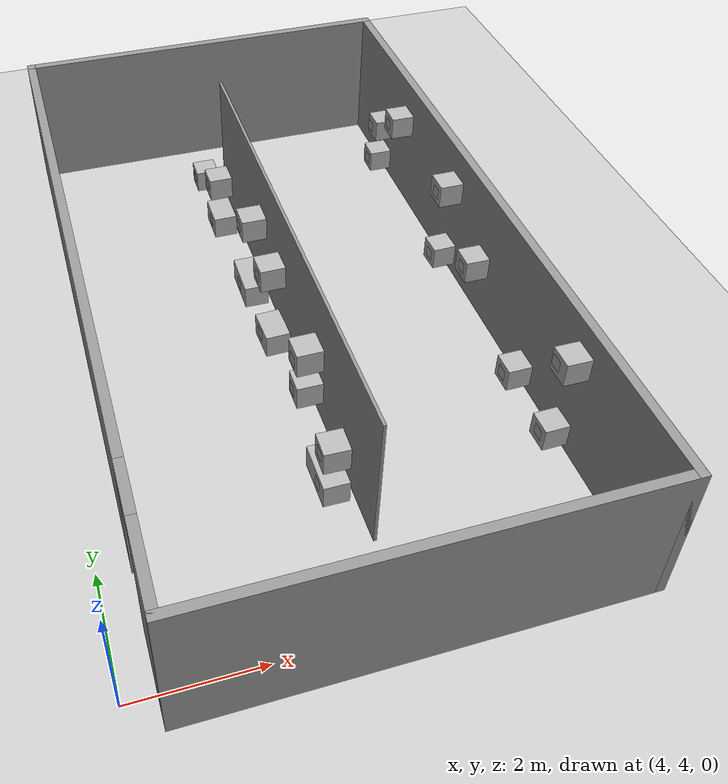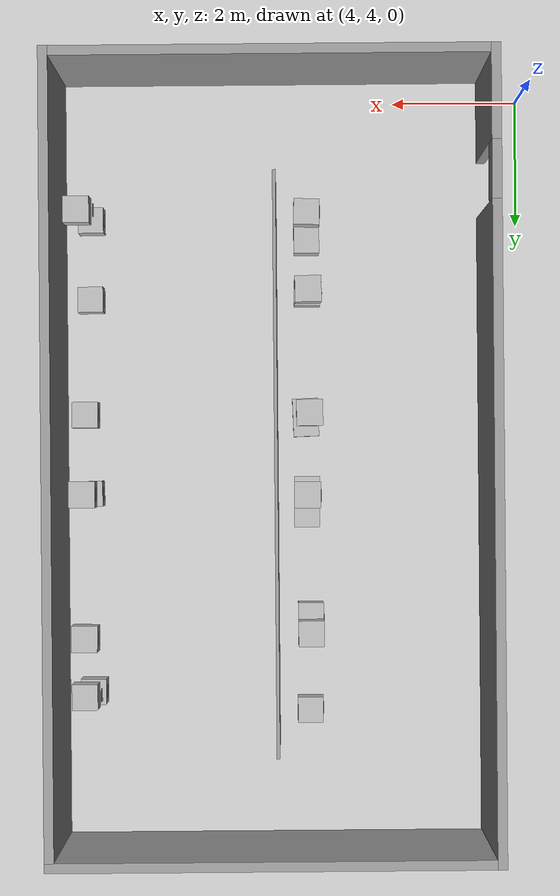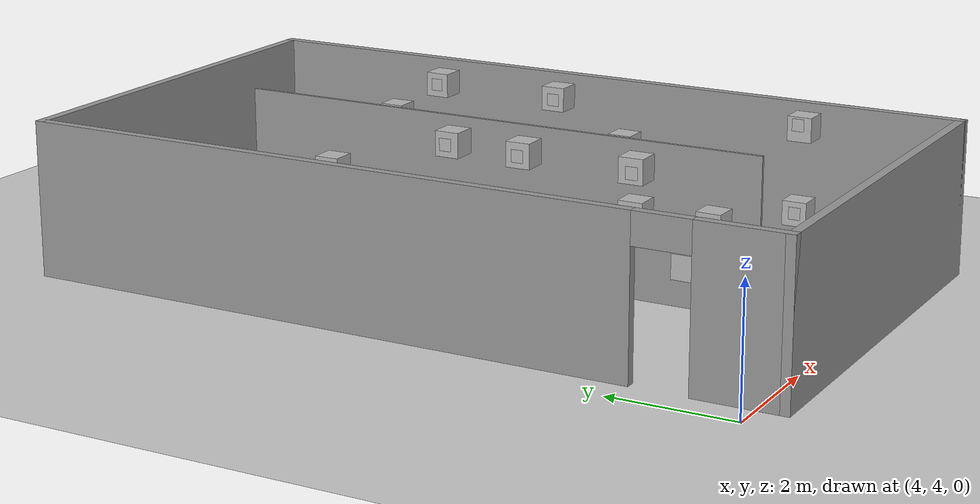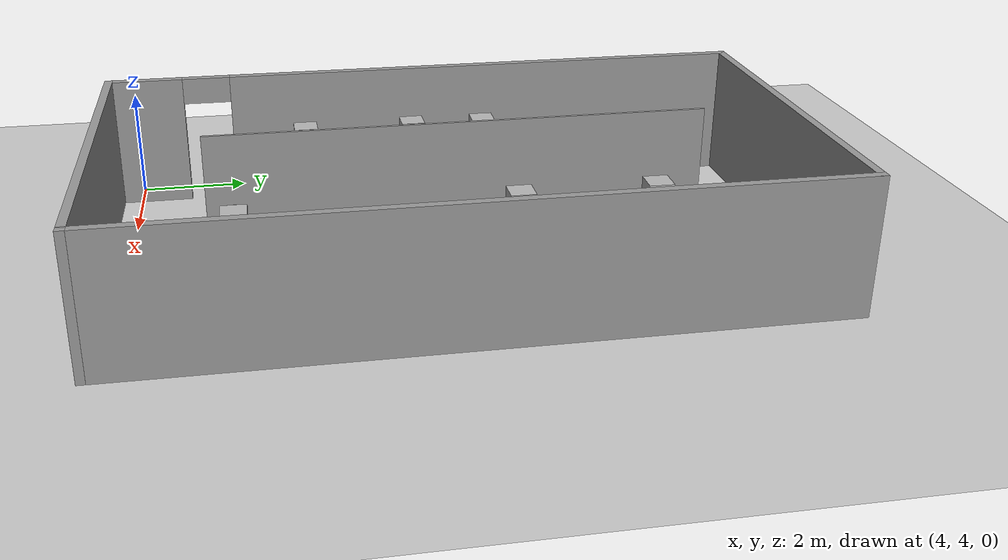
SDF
<sdf version="1.6">
 <world name="default">
  <plugin name="ros_interface_plugin" filename="librotors_gazebo_ros_interface_plugin.so"/>
  <light name="sun" type="directional">
   <pose>10 10 10 0 -0 0</pose>
   <diffuse>0.8 0.8 0.8 1</diffuse>
   <specular>0.2 0.2 0.2 1</specular>
   <attenuation>
    <range>1000</range>
    <constant>0.9</constant>
    <linear>0.01</linear>
    <quadratic>0.001</quadratic>
   </attenuation>
   <direction>-0.5 0.1 -0.9</direction>
  </light>
  <model name="ground_plane">
   <static>1</static>
   <link name="link">
    <collision name="collision">
     <geometry><plane><normal>0 0 1</normal><size>300 300</size></plane></geometry>
     <surface>
      <contact><collide_bitmask>65535</collide_bitmask></contact>
      <friction><ode><mu>100</mu><mu2>50</mu2></ode></friction>
     </surface>
    </collision>
    <visual name="visual">
     <geometry><plane><normal>0 0 1</normal><size>100 100</size></plane></geometry>
     <material>
      <script><uri>file://media/materials/scripts/gazebo.material</uri><name>Gazebo/Grey</name></script>
     </material>
    </visual>
   </link>
  </model>
  <gravity>0 0 -9.8</gravity>
  <magnetic_field>6e-06 2.3e-05 -4.2e-05</magnetic_field>
  <atmosphere type="adiabatic"/>
  <physics name="default_physics" default="0" type="ode">
   <max_step_size>0.001</max_step_size>
   <real_time_factor>1</real_time_factor>
   <real_time_update_rate>1000</real_time_update_rate>
  </physics>
  <scene><ambient>0.4 0.4 0.4 1</ambient><background>0.7 0.7 0.7 1</background><shadows>1</shadows></scene>
  <spherical_coordinates>
   <surface_model>EARTH_WGS84</surface_model>
   <latitude_deg>0</latitude_deg>
   <longitude_deg>0</longitude_deg>
   <elevation>0</elevation>
   <heading_deg>0</heading_deg>
  </spherical_coordinates>
  <audio><device>default</device></audio>
  <model name="CuboQR5">
   <link name="link">
    <pose>1.40986 -0.258688 0.90666 0 -0 -0.075519</pose>
    <inertial>
     <mass>0.39</mass>
     <inertia><ixx>0.00058</ixx><ixy>0</ixy><ixz>0</ixz><iyy>0.00058</iyy><iyz>0</iyz><izz>0.00019</izz></inertia>
    </inertial>
    <visual name="visual">
     <geometry><box><size>0.4 0.4 0.4</size></box></geometry>
     <material>
      <script>
       <uri>model://Caja/materials/scripts</uri>
       <uri>model://Caja/materials/textures</uri>
       <name>Caja/Diffuse</name>
      </script>
      <shader type="pixel"/>
     </material>
    </visual>
    <collision name="collision">
     <geometry><box><size>0.4 0.4 0.4</size></box></geometry>
     <surface>
      <friction>
       <ode><mu>1</mu><mu2>1</mu2><fdir1>0 0 0</fdir1><slip1>0</slip1><slip2>0</slip2></ode>
       <torsional>
        <coefficient>1</coefficient>
        <patch_radius>0</patch_radius>
        <surface_radius>0</surface_radius>
        <use_patch_radius>1</use_patch_radius>
        <ode><slip>0</slip></ode>
       </torsional>
      </friction>
      <bounce><restitution_coefficient>0</restitution_coefficient><threshold>1e+06</threshold></bounce>
      <contact>
       <collide_without_contact>0</collide_without_contact>
       <collide_without_contact_bitmask>1</collide_without_contact_bitmask>
       <collide_bitmask>1</collide_bitmask>
       <ode>
        <soft_cfm>0</soft_cfm>
        <soft_erp>0.2</soft_erp>
        <kp>1e+13</kp>
        <kd>1</kd>
        <max_vel>0.01</max_vel>
        <min_depth>0</min_depth>
       </ode>
       <bullet>
        <split_impulse>1</split_impulse>
        <split_impulse_penetration_threshold>-0.01</split_impulse_penetration_threshold>
        <soft_cfm>0</soft_cfm>
        <soft_erp>0.2</soft_erp>
        <kp>1e+13</kp>
        <kd>1</kd>
       </bullet>
      </contact>
     </surface>
    </collision>
   </link>
   <static>0</static>
   <pose>5.99954 13.9136 -0.05574 2.1e-05 -1.4e-05 0.072613</pose>
  </model>
  <model name="CuboQR32">
   <link name="link">
    <pose>0.09504 -2.80651 0.918216 0 0 -0.549246</pose>
    <inertial>
     <mass>0.39</mass>
     <inertia><ixx>0.00058</ixx><ixy>0</ixy><ixz>0</ixz><iyy>0.00058</iyy><iyz>0</iyz><izz>0.00019</izz></inertia>
    </inertial>
    <visual name="visual">
     <geometry><box><size>0.4 0.6 0.4</size></box></geometry>
     <material>
      <script>
       <uri>model://Caja/materials/scripts</uri>
       <uri>model://Caja/materials/textures</uri>
       <name>Caja/Diffuse</name>
      </script>
      <shader type="pixel"/>
     </material>
    </visual>
    <collision name="collision">
     <geometry><box><size>0.4 0.6 0.4</size></box></geometry>
     <surface>
      <friction>
       <ode><mu>1</mu><mu2>1</mu2><fdir1>0 0 0</fdir1><slip1>0</slip1><slip2>0</slip2></ode>
       <torsional>
        <coefficient>1</coefficient>
        <patch_radius>0</patch_radius>
        <surface_radius>0</surface_radius>
        <use_patch_radius>1</use_patch_radius>
        <ode><slip>0</slip></ode>
       </torsional>
      </friction>
      <bounce><restitution_coefficient>0</restitution_coefficient><threshold>1e+06</threshold></bounce>
      <contact>
       <collide_without_contact>0</collide_without_contact>
       <collide_without_contact_bitmask>1</collide_without_contact_bitmask>
       <collide_bitmask>1</collide_bitmask>
       <ode>
        <soft_cfm>0</soft_cfm>
        <soft_erp>0.2</soft_erp>
        <kp>1e+13</kp>
        <kd>1</kd>
        <max_vel>0.01</max_vel>
        <min_depth>0</min_depth>
       </ode>
       <bullet>
        <split_impulse>1</split_impulse>
        <split_impulse_penetration_threshold>-0.01</split_impulse_penetration_threshold>
        <soft_cfm>0</soft_cfm>
        <soft_erp>0.2</soft_erp>
        <kp>1e+13</kp>
        <kd>1</kd>
       </bullet>
      </contact>
     </surface>
    </collision>
   </link>
   <static>0</static>
   <pose>5.86345 14.7048 -0.067277 2e-06 -2e-06 0.548822</pose>
  </model>
  <model name="CuboQR6">
   <link name="link">
    <pose>0.57577 -1.62645 -1.0907 0 -0 0.780081</pose>
    <inertial>
     <mass>0.39</mass>
     <inertia><ixx>0.00058</ixx><ixy>0</ixy><ixz>0</ixz><iyy>0.00058</iyy><iyz>0</iyz><izz>0.00019</izz></inertia>
    </inertial>
    <visual name="visual">
     <geometry><box><size>0.4 0.4 0.4</size></box></geometry>
     <material>
      <script>
       <uri>model://Caja/materials/scripts</uri>
       <uri>model://Caja/materials/textures</uri>
       <name>Caja/Diffuse</name>
      </script>
      <shader type="pixel"/>
     </material>
    </visual>
    <collision name="collision">
     <geometry><box><size>0.4 0.4 0.4</size></box></geometry>
     <surface>
      <friction>
       <ode><mu>1</mu><mu2>1</mu2><fdir1>0 0 0</fdir1><slip1>0</slip1><slip2>0</slip2></ode>
       <torsional>
        <coefficient>1</coefficient>
        <patch_radius>0</patch_radius>
        <surface_radius>0</surface_radius>
        <use_patch_radius>1</use_patch_radius>
        <ode><slip>0</slip></ode>
       </torsional>
      </friction>
      <bounce><restitution_coefficient>0</restitution_coefficient><threshold>1e+06</threshold></bounce>
      <contact>
       <collide_without_contact>0</collide_without_contact>
       <collide_without_contact_bitmask>1</collide_without_contact_bitmask>
       <collide_bitmask>1</collide_bitmask>
       <ode>
        <soft_cfm>0</soft_cfm>
        <soft_erp>0.2</soft_erp>
        <kp>1e+13</kp>
        <kd>1</kd>
        <max_vel>0.01</max_vel>
        <min_depth>0</min_depth>
       </ode>
       <bullet>
        <split_impulse>1</split_impulse>
        <split_impulse_penetration_threshold>-0.01</split_impulse_penetration_threshold>
        <soft_cfm>0</soft_cfm>
        <soft_erp>0.2</soft_erp>
        <kp>1e+13</kp>
        <kd>1</kd>
       </bullet>
      </contact>
     </surface>
    </collision>
   </link>
   <static>0</static>
   <pose>5.853 11.7526 0.447654 -3.14157 1.9e-05 -0.785249</pose>
  </model>
  <model name="CuboQR8">
   <link name="link">
    <pose>1.33161 0.916406 0.895911 -0 -0 -0.362899</pose>
    <inertial>
     <mass>0.39</mass>
     <inertia><ixx>0.00058</ixx><ixy>0</ixy><ixz>0</ixz><iyy>0.00058</iyy><iyz>0</iyz><izz>0.00019</izz></inertia>
    </inertial>
    <visual name="visual">
     <geometry><box><size>0.4 0.8 0.4</size></box></geometry>
     <material>
      <script>
       <uri>model://Caja/materials/scripts</uri>
       <uri>model://Caja/materials/textures</uri>
       <name>Caja/Diffuse</name>
      </script>
      <shader type="pixel"/>
     </material>
    </visual>
    <collision name="collision">
     <geometry><box><size>0.4 0.8 0.4</size></box></geometry>
     <surface>
      <friction>
       <ode><mu>1</mu><mu2>1</mu2><fdir1>0 0 0</fdir1><slip1>0</slip1><slip2>0</slip2></ode>
       <torsional>
        <coefficient>1</coefficient>
        <patch_radius>0</patch_radius>
        <surface_radius>0</surface_radius>
        <use_patch_radius>1</use_patch_radius>
        <ode><slip>0</slip></ode>
       </torsional>
      </friction>
      <bounce><restitution_coefficient>0</restitution_coefficient><threshold>1e+06</threshold></bounce>
      <contact>
       <collide_without_contact>0</collide_without_contact>
       <collide_without_contact_bitmask>1</collide_without_contact_bitmask>
       <collide_bitmask>1</collide_bitmask>
       <ode>
        <soft_cfm>0</soft_cfm>
        <soft_erp>0.2</soft_erp>
        <kp>1e+13</kp>
        <kd>1</kd>
        <max_vel>0.01</max_vel>
        <min_depth>0</min_depth>
       </ode>
       <bullet>
        <split_impulse>1</split_impulse>
        <split_impulse_penetration_threshold>-0.01</split_impulse_penetration_threshold>
        <soft_cfm>0</soft_cfm>
        <soft_erp>0.2</soft_erp>
        <kp>1e+13</kp>
        <kd>1</kd>
       </bullet>
      </contact>
     </surface>
    </collision>
   </link>
   <static>0</static>
   <pose>6.52855 9.13954 -0.044975 -9e-06 -4e-06 0.354617</pose>
  </model>
  <model name="CuboQR30">
   <link name="link">
    <pose>1.4917 0.506438 0.904274 0 -0 0.004736</pose>
    <inertial>
     <mass>0.39</mass>
     <inertia><ixx>0.00058</ixx><ixy>0</ixy><ixz>0</ixz><iyy>0.00058</iyy><iyz>0</iyz><izz>0.00019</izz></inertia>
    </inertial>
    <visual name="visual">
     <geometry><box><size>0.4 0.6 0.4</size></box></geometry>
     <material>
      <script>
       <uri>model://Caja/materials/scripts</uri>
       <uri>model://Caja/materials/textures</uri>
       <name>Caja/Diffuse</name>
      </script>
      <shader type="pixel"/>
     </material>
    </visual>
    <collision name="collision">
     <geometry><box><size>0.4 0.6 0.4</size></box></geometry>
     <surface>
      <friction>
       <ode><mu>1</mu><mu2>1</mu2><fdir1>0 0 0</fdir1><slip1>0</slip1><slip2>0</slip2></ode>
       <torsional>
        <coefficient>1</coefficient>
        <patch_radius>0</patch_radius>
        <surface_radius>0</surface_radius>
        <use_patch_radius>1</use_patch_radius>
        <ode><slip>0</slip></ode>
       </torsional>
      </friction>
      <bounce><restitution_coefficient>0</restitution_coefficient><threshold>1e+06</threshold></bounce>
      <contact>
       <collide_without_contact>0</collide_without_contact>
       <collide_without_contact_bitmask>1</collide_without_contact_bitmask>
       <collide_bitmask>1</collide_bitmask>
       <ode>
        <soft_cfm>0</soft_cfm>
        <soft_erp>0.2</soft_erp>
        <kp>1e+13</kp>
        <kd>1</kd>
        <max_vel>0.01</max_vel>
        <min_depth>0</min_depth>
       </ode>
       <bullet>
        <split_impulse>1</split_impulse>
        <split_impulse_penetration_threshold>-0.01</split_impulse_penetration_threshold>
        <soft_cfm>0</soft_cfm>
        <soft_erp>0.2</soft_erp>
        <kp>1e+13</kp>
        <kd>1</kd>
       </bullet>
      </contact>
     </surface>
    </collision>
   </link>
   <static>0</static>
   <pose>5.99382 8.57393 -0.053336 -1.7e-05 2e-06 0.031771</pose>
  </model>
  <model name="CuboQR9">
   <link name="link">
    <pose>-2.00082 0.70939 2.01363 0.229474 0.007293 0.002021</pose>
    <inertial>
     <mass>0.39</mass>
     <inertia><ixx>0.00058</ixx><ixy>0</ixy><ixz>0</ixz><iyy>0.00058</iyy><iyz>0</iyz><izz>0.00019</izz></inertia>
    </inertial>
    <visual name="visual">
     <geometry><box><size>0.4 0.4 0.4</size></box></geometry>
     <material>
      <script>
       <uri>model://Caja/materials/scripts</uri>
       <uri>model://Caja/materials/textures</uri>
       <name>Caja/Diffuse</name>
      </script>
      <shader type="pixel"/>
     </material>
    </visual>
    <collision name="collision">
     <geometry><box><size>0.4 0.4 0.4</size></box></geometry>
     <surface>
      <friction>
       <ode><mu>1</mu><mu2>1</mu2><fdir1>0 0 0</fdir1><slip1>0</slip1><slip2>0</slip2></ode>
       <torsional>
        <coefficient>1</coefficient>
        <patch_radius>0</patch_radius>
        <surface_radius>0</surface_radius>
        <use_patch_radius>1</use_patch_radius>
        <ode><slip>0</slip></ode>
       </torsional>
      </friction>
      <bounce><restitution_coefficient>0</restitution_coefficient><threshold>1e+06</threshold></bounce>
      <contact>
       <collide_without_contact>0</collide_without_contact>
       <collide_without_contact_bitmask>1</collide_without_contact_bitmask>
       <collide_bitmask>1</collide_bitmask>
       <ode>
        <soft_cfm>0</soft_cfm>
        <soft_erp>0.2</soft_erp>
        <kp>1e+13</kp>
        <kd>1</kd>
        <max_vel>0.01</max_vel>
        <min_depth>0</min_depth>
       </ode>
       <bullet>
        <split_impulse>1</split_impulse>
        <split_impulse_penetration_threshold>-0.01</split_impulse_penetration_threshold>
        <soft_cfm>0</soft_cfm>
        <soft_erp>0.2</soft_erp>
        <kp>1e+13</kp>
        <kd>1</kd>
       </bullet>
      </contact>
     </surface>
    </collision>
   </link>
   <static>0</static>
   <pose>6.24234 10.8446 0.190057 -0.27111 1.56321 -1.59622</pose>
  </model>
  <model name="CuboQR4">
   <link name="link">
    <pose>1.4541 1.7784 0.940521 0 -0 0</pose>
    <inertial>
     <mass>0.39</mass>
     <inertia><ixx>0.00058</ixx><ixy>0</ixy><ixz>0</ixz><iyy>0.00058</iyy><iyz>0</iyz><izz>0.00019</izz></inertia>
    </inertial>
    <visual name="visual">
     <geometry><box><size>0.4 0.8 0.4</size></box></geometry>
     <material>
      <script>
       <uri>model://Caja/materials/scripts</uri>
       <uri>model://Caja/materials/textures</uri>
       <name>Caja/Diffuse</name>
      </script>
      <shader type="pixel"/>
     </material>
    </visual>
    <collision name="collision">
     <geometry><box><size>0.4 0.8 0.4</size></box></geometry>
     <surface>
      <friction>
       <ode><mu>1</mu><mu2>1</mu2><fdir1>0 0 0</fdir1><slip1>0</slip1><slip2>0</slip2></ode>
       <torsional>
        <coefficient>1</coefficient>
        <patch_radius>0</patch_radius>
        <surface_radius>0</surface_radius>
        <use_patch_radius>1</use_patch_radius>
        <ode><slip>0</slip></ode>
       </torsional>
      </friction>
      <bounce><restitution_coefficient>0</restitution_coefficient><threshold>1e+06</threshold></bounce>
      <contact>
       <collide_without_contact>0</collide_without_contact>
       <collide_without_contact_bitmask>1</collide_without_contact_bitmask>
       <collide_bitmask>1</collide_bitmask>
       <ode>
        <soft_cfm>0</soft_cfm>
        <soft_erp>0.2</soft_erp>
        <kp>1e+13</kp>
        <kd>1</kd>
        <max_vel>0.01</max_vel>
        <min_depth>0</min_depth>
       </ode>
       <bullet>
        <split_impulse>1</split_impulse>
        <split_impulse_penetration_threshold>-0.01</split_impulse_penetration_threshold>
        <soft_cfm>0</soft_cfm>
        <soft_erp>0.2</soft_erp>
        <kp>1e+13</kp>
        <kd>1</kd>
       </bullet>
      </contact>
     </surface>
    </collision>
   </link>
   <static>0</static>
   <pose>5.98514 4.34705 -0.089558 -1.7e-05 -1e-06 0.001748</pose>
  </model>
  <model name="CuboQR2">
   <link name="link">
    <pose>1.59419 -0.501465 1.58657 -0 -0 -0.004218</pose>
    <inertial>
     <mass>0.39</mass>
     <inertia><ixx>0.00058</ixx><ixy>0</ixy><ixz>0</ixz><iyy>0.00058</iyy><iyz>0</iyz><izz>0.00019</izz></inertia>
    </inertial>
    <visual name="visual">
     <geometry><box><size>0.4 0.4 0.4</size></box></geometry>
     <material>
      <script>
       <uri>model://Caja/materials/scripts</uri>
       <uri>model://Caja/materials/textures</uri>
       <name>Caja/Diffuse</name>
      </script>
      <shader type="pixel"/>
     </material>
    </visual>
    <collision name="collision">
     <geometry><box><size>0.4 0.4 0.4</size></box></geometry>
     <surface>
      <friction>
       <ode><mu>1</mu><mu2>1</mu2><fdir1>0 0 0</fdir1><slip1>0</slip1><slip2>0</slip2></ode>
       <torsional>
        <coefficient>1</coefficient>
        <patch_radius>0</patch_radius>
        <surface_radius>0</surface_radius>
        <use_patch_radius>1</use_patch_radius>
        <ode><slip>0</slip></ode>
       </torsional>
      </friction>
      <bounce><restitution_coefficient>0</restitution_coefficient><threshold>1e+06</threshold></bounce>
      <contact>
       <collide_without_contact>0</collide_without_contact>
       <collide_without_contact_bitmask>1</collide_without_contact_bitmask>
       <collide_bitmask>1</collide_bitmask>
       <ode>
        <soft_cfm>0</soft_cfm>
        <soft_erp>0.2</soft_erp>
        <kp>1e+13</kp>
        <kd>1</kd>
        <max_vel>0.01</max_vel>
        <min_depth>0</min_depth>
       </ode>
       <bullet>
        <split_impulse>1</split_impulse>
        <split_impulse_penetration_threshold>-0.01</split_impulse_penetration_threshold>
        <soft_cfm>0</soft_cfm>
        <soft_erp>0.2</soft_erp>
        <kp>1e+13</kp>
        <kd>1</kd>
       </bullet>
      </contact>
     </surface>
    </collision>
   </link>
   <static>0</static>
   <pose>5.85292 6.48203 -0.048167 7e-06 9e-06 -0.01717</pose>
  </model>
  <model name="CuboQR3">
   <link name="link">
    <pose>1.72852 -0.054688 2.25892 0 -0 0.030523</pose>
    <inertial>
     <mass>0.39</mass>
     <inertia><ixx>0.00058</ixx><ixy>0</ixy><ixz>0</ixz><iyy>0.00058</iyy><iyz>0</iyz><izz>0.00019</izz></inertia>
    </inertial>
    <visual name="visual">
     <geometry><box><size>0.4 0.4 0.4</size></box></geometry>
     <material>
      <script>
       <uri>model://Caja/materials/scripts</uri>
       <uri>model://Caja/materials/textures</uri>
       <name>Caja/Diffuse</name>
      </script>
      <shader type="pixel"/>
     </material>
    </visual>
    <collision name="collision">
     <geometry><box><size>0.4 0.4 0.4</size></box></geometry>
     <surface>
      <friction>
       <ode><mu>1</mu><mu2>1</mu2><fdir1>0 0 0</fdir1><slip1>0</slip1><slip2>0</slip2></ode>
       <torsional>
        <coefficient>1</coefficient>
        <patch_radius>0</patch_radius>
        <surface_radius>0</surface_radius>
        <use_patch_radius>1</use_patch_radius>
        <ode><slip>0</slip></ode>
       </torsional>
      </friction>
      <bounce><restitution_coefficient>0</restitution_coefficient><threshold>1e+06</threshold></bounce>
      <contact>
       <collide_without_contact>0</collide_without_contact>
       <collide_without_contact_bitmask>1</collide_without_contact_bitmask>
       <collide_bitmask>1</collide_bitmask>
       <ode>
        <soft_cfm>0</soft_cfm>
        <soft_erp>0.2</soft_erp>
        <kp>1e+13</kp>
        <kd>1</kd>
        <max_vel>0.01</max_vel>
        <min_depth>0</min_depth>
       </ode>
       <bullet>
        <split_impulse>1</split_impulse>
        <split_impulse_penetration_threshold>-0.01</split_impulse_penetration_threshold>
        <soft_cfm>0</soft_cfm>
        <soft_erp>0.2</soft_erp>
        <kp>1e+13</kp>
        <kd>1</kd>
       </bullet>
      </contact>
     </surface>
    </collision>
   </link>
   <static>0</static>
   <pose>5.70295 7.29191 -0.054824 -7e-06 3e-06 -0.019304</pose>
  </model>
  <model name="Plano">
   <link name="link">
    <gravity>0</gravity>
    <pose>-0.103478 0.986463 0.8108 0 -0 0</pose>
    <inertial>
     <mass>1e-06</mass>
     <inertia><ixx>0.00058</ixx><ixy>0</ixy><ixz>0</ixz><iyy>0.00058</iyy><iyz>0</iyz><izz>0.00019</izz></inertia>
    </inertial>
    <visual name="visual">
     <geometry><box><size>0.2 1e-06 0.2</size></box></geometry>
     <material>
      <script>
       <uri>model://Plano/materials/scripts</uri>
       <uri>model://Plano/materials/textures</uri>
       <name>Plano/Diffuse</name>
      </script>
      <shader type="pixel"/>
     </material>
     <cast_shadows>0</cast_shadows>
    </visual>
    <collision name="collision">
     <geometry><box><size>0.2 1e-06 0.2</size></box></geometry>
     <surface>
      <friction>
       <ode><mu>1</mu><mu2>1</mu2><fdir1>0 0 0</fdir1><slip1>0</slip1><slip2>0</slip2></ode>
       <torsional>
        <coefficient>1</coefficient>
        <patch_radius>0</patch_radius>
        <surface_radius>0</surface_radius>
        <use_patch_radius>1</use_patch_radius>
        <ode><slip>0</slip></ode>
       </torsional>
      </friction>
      <bounce><restitution_coefficient>0</restitution_coefficient><threshold>1e+06</threshold></bounce>
      <contact>
       <collide_without_contact>0</collide_without_contact>
       <collide_without_contact_bitmask>1</collide_without_contact_bitmask>
       <collide_bitmask>1</collide_bitmask>
       <ode>
        <soft_cfm>0</soft_cfm>
        <soft_erp>0.2</soft_erp>
        <kp>1e+13</kp>
        <kd>1</kd>
        <max_vel>0.01</max_vel>
        <min_depth>0</min_depth>
       </ode>
       <bullet>
        <split_impulse>1</split_impulse>
        <split_impulse_penetration_threshold>-0.01</split_impulse_penetration_threshold>
        <soft_cfm>0</soft_cfm>
        <soft_erp>0.2</soft_erp>
        <kp>1e+13</kp>
        <kd>1</kd>
       </bullet>
      </contact>
     </surface>
    </collision>
   </link>
   <static>0</static>
   <pose>6.24495 5.89293 0.053748 0 0 -1.57043</pose>
  </model>
  <model name="Plano2">
   <link name="link">
    <gravity>0</gravity>
    <pose>0.45527 1.12131 0.660976 0 -0 0</pose>
    <inertial>
     <mass>1e-06</mass>
     <inertia><ixx>0.00058</ixx><ixy>0</ixy><ixz>0</ixz><iyy>0.00058</iyy><iyz>0</iyz><izz>0.00019</izz></inertia>
    </inertial>
    <visual name="visual">
     <geometry><box><size>0.2 1e-06 0.2</size></box></geometry>
     <material>
      <script>
       <uri>model://Plano2/materials/scripts</uri>
       <uri>model://Plano2/materials/textures</uri>
       <name>Plano2/Diffuse</name>
      </script>
      <shader type="pixel"/>
     </material>
     <cast_shadows>0</cast_shadows>
    </visual>
    <collision name="collision">
     <geometry><box><size>0.2 1e-06 0.2</size></box></geometry>
     <surface>
      <friction>
       <ode><mu>1</mu><mu2>1</mu2><fdir1>0 0 0</fdir1><slip1>0</slip1><slip2>0</slip2></ode>
       <torsional>
        <coefficient>1</coefficient>
        <patch_radius>0</patch_radius>
        <surface_radius>0</surface_radius>
        <use_patch_radius>1</use_patch_radius>
        <ode><slip>0</slip></ode>
       </torsional>
      </friction>
      <bounce><restitution_coefficient>0</restitution_coefficient><threshold>1e+06</threshold></bounce>
      <contact>
       <collide_without_contact>0</collide_without_contact>
       <collide_without_contact_bitmask>1</collide_without_contact_bitmask>
       <collide_bitmask>1</collide_bitmask>
       <ode>
        <soft_cfm>0</soft_cfm>
        <soft_erp>0.2</soft_erp>
        <kp>1e+13</kp>
        <kd>1</kd>
        <max_vel>0.01</max_vel>
        <min_depth>0</min_depth>
       </ode>
       <bullet>
        <split_impulse>1</split_impulse>
        <split_impulse_penetration_threshold>-0.01</split_impulse_penetration_threshold>
        <soft_cfm>0</soft_cfm>
        <soft_erp>0.2</soft_erp>
        <kp>1e+13</kp>
        <kd>1</kd>
       </bullet>
      </contact>
     </surface>
    </collision>
   </link>
   <static>0</static>
   <pose>6.11634 6.41923 0.907634 0 0 -1.5813</pose>
  </model>
  <model name="Caja">
   <link name="link">
    <pose>1.53848 1.3495 -1.37205 0.031423 0.044064 -0.000927</pose>
    <inertial>
     <mass>0.39</mass>
     <inertia><ixx>0.00058</ixx><ixy>0</ixy><ixz>0</ixz><iyy>0.00058</iyy><iyz>0</iyz><izz>0.00019</izz></inertia>
    </inertial>
    <visual name="visual">
     <geometry><box><size>0.4 0.4 0.4</size></box></geometry>
     <material>
      <script>
       <uri>model://Caja/materials/scripts</uri>
       <uri>model://Caja/materials/textures</uri>
       <name>Caja/Diffuse</name>
      </script>
      <shader type="pixel"/>
     </material>
    </visual>
    <collision name="collision">
     <geometry><box><size>0.4 0.4 0.4</size></box></geometry>
     <surface>
      <friction>
       <ode><mu>1</mu><mu2>1</mu2><fdir1>0 0 0</fdir1><slip1>0</slip1><slip2>0</slip2></ode>
       <torsional>
        <coefficient>1</coefficient>
        <patch_radius>0</patch_radius>
        <surface_radius>0</surface_radius>
        <use_patch_radius>1</use_patch_radius>
        <ode><slip>0</slip></ode>
       </torsional>
      </friction>
      <bounce><restitution_coefficient>0</restitution_coefficient><threshold>1e+06</threshold></bounce>
      <contact>
       <collide_without_contact>0</collide_without_contact>
       <collide_without_contact_bitmask>1</collide_without_contact_bitmask>
       <collide_bitmask>1</collide_bitmask>
       <ode>
        <soft_cfm>0</soft_cfm>
        <soft_erp>0.2</soft_erp>
        <kp>1e+13</kp>
        <kd>1</kd>
        <max_vel>0.01</max_vel>
        <min_depth>0</min_depth>
       </ode>
       <bullet>
        <split_impulse>1</split_impulse>
        <split_impulse_penetration_threshold>-0.01</split_impulse_penetration_threshold>
        <soft_cfm>0</soft_cfm>
        <soft_erp>0.2</soft_erp>
        <kp>1e+13</kp>
        <kd>1</kd>
       </bullet>
      </contact>
     </surface>
    </collision>
   </link>
   <static>0</static>
   <pose>5.83979 5.86875 0.229074 1.53941 -0.002301 -0.046636</pose>
  </model>
  <model name="Plano3">
   <link name="link">
    <gravity>0</gravity>
    <pose>-0.321438 0.622252 1.59842 0 -0 0</pose>
    <inertial>
     <mass>1e-06</mass>
     <inertia><ixx>0.00058</ixx><ixy>0</ixy><ixz>0</ixz><iyy>0.00058</iyy><iyz>0</iyz><izz>0.00019</izz></inertia>
    </inertial>
    <visual name="visual">
     <geometry><box><size>0.2 1e-06 0.2</size></box></geometry>
     <material>
      <script>
       <uri>model://Plano3/materials/scripts</uri>
       <uri>model://Plano3/materials/textures</uri>
       <name>Plano3/Diffuse</name>
      </script>
      <shader type="pixel"/>
     </material>
     <cast_shadows>0</cast_shadows>
    </visual>
    <collision name="collision">
     <geometry><box><size>0.2 1e-06 0.2</size></box></geometry>
     <surface>
      <friction>
       <ode><mu>1</mu><mu2>1</mu2><fdir1>0 0 0</fdir1><slip1>0</slip1><slip2>0</slip2></ode>
       <torsional>
        <coefficient>1</coefficient>
        <patch_radius>0</patch_radius>
        <surface_radius>0</surface_radius>
        <use_patch_radius>1</use_patch_radius>
        <ode><slip>0</slip></ode>
       </torsional>
      </friction>
      <bounce><restitution_coefficient>0</restitution_coefficient><threshold>1e+06</threshold></bounce>
      <contact>
       <collide_without_contact>0</collide_without_contact>
       <collide_without_contact_bitmask>1</collide_without_contact_bitmask>
       <collide_bitmask>1</collide_bitmask>
       <ode>
        <soft_cfm>0</soft_cfm>
        <soft_erp>0.2</soft_erp>
        <kp>1e+13</kp>
        <kd>1</kd>
        <max_vel>0.01</max_vel>
        <min_depth>0</min_depth>
       </ode>
       <bullet>
        <split_impulse>1</split_impulse>
        <split_impulse_penetration_threshold>-0.01</split_impulse_penetration_threshold>
        <soft_cfm>0</soft_cfm>
        <soft_erp>0.2</soft_erp>
        <kp>1e+13</kp>
        <kd>1</kd>
       </bullet>
      </contact>
     </surface>
    </collision>
   </link>
   <static>0</static>
   <pose>6.60144 6.90216 -0.05097 0 0 -1.57531</pose>
  </model>
  <model name="Plano4">
   <link name="link">
    <gravity>0</gravity>
    <pose>0.342529 1.36427 1.91258 0 -0 0.032722</pose>
    <inertial>
     <mass>1e-06</mass>
     <inertia><ixx>0.00058</ixx><ixy>0</ixy><ixz>0</ixz><iyy>0.00058</iyy><iyz>0</iyz><izz>0.00019</izz></inertia>
    </inertial>
    <visual name="visual">
     <geometry><box><size>0.2 1e-06 0.2</size></box></geometry>
     <material>
      <script>
       <uri>model://Plano4/materials/scripts</uri>
       <uri>model://Plano4/materials/textures</uri>
       <name>Plano4/Diffuse</name>
      </script>
      <shader type="pixel"/>
     </material>
     <cast_shadows>0</cast_shadows>
    </visual>
    <collision name="collision">
     <geometry><box><size>0.2 1e-06 0.2</size></box></geometry>
     <surface>
      <friction>
       <ode><mu>1</mu><mu2>1</mu2><fdir1>0 0 0</fdir1><slip1>0</slip1><slip2>0</slip2></ode>
       <torsional>
        <coefficient>1</coefficient>
        <patch_radius>0</patch_radius>
        <surface_radius>0</surface_radius>
        <use_patch_radius>1</use_patch_radius>
        <ode><slip>0</slip></ode>
       </torsional>
      </friction>
      <bounce><restitution_coefficient>0</restitution_coefficient><threshold>1e+06</threshold></bounce>
      <contact>
       <collide_without_contact>0</collide_without_contact>
       <collide_without_contact_bitmask>1</collide_without_contact_bitmask>
       <collide_bitmask>1</collide_bitmask>
       <ode>
        <soft_cfm>0</soft_cfm>
        <soft_erp>0.2</soft_erp>
        <kp>1e+13</kp>
        <kd>1</kd>
        <max_vel>0.01</max_vel>
        <min_depth>0</min_depth>
       </ode>
       <bullet>
        <split_impulse>1</split_impulse>
        <split_impulse_penetration_threshold>-0.01</split_impulse_penetration_threshold>
        <soft_cfm>0</soft_cfm>
        <soft_erp>0.2</soft_erp>
        <kp>1e+13</kp>
        <kd>1</kd>
       </bullet>
      </contact>
     </surface>
    </collision>
   </link>
   <static>0</static>
   <pose>5.86012 7.53798 0.26346 0 0 -1.5802</pose>
  </model>
  <model name="Plano30">
   <link name="link">
    <gravity>0</gravity>
    <pose>0.142948 1.63527 -0.030652 0 -0 0.095189</pose>
    <inertial>
     <mass>1e-06</mass>
     <inertia><ixx>0.00058</ixx><ixy>0</ixy><ixz>0</ixz><iyy>0.00058</iyy><iyz>0</iyz><izz>0.00019</izz></inertia>
    </inertial>
    <visual name="visual">
     <geometry><box><size>0.2 1e-06 0.2</size></box></geometry>
     <material>
      <script>
       <uri>model://Plano30/materials/scripts</uri>
       <uri>model://Plano30/materials/textures</uri>
       <name>Plano30/Diffuse</name>
      </script>
      <shader type="pixel"/>
     </material>
     <cast_shadows>0</cast_shadows>
    </visual>
    <collision name="collision">
     <geometry><box><size>0.2 1e-06 0.2</size></box></geometry>
     <surface>
      <friction>
       <ode><mu>1</mu><mu2>1</mu2><fdir1>0 0 0</fdir1><slip1>0</slip1><slip2>0</slip2></ode>
       <torsional>
        <coefficient>1</coefficient>
        <patch_radius>0</patch_radius>
        <surface_radius>0</surface_radius>
        <use_patch_radius>1</use_patch_radius>
        <ode><slip>0</slip></ode>
       </torsional>
      </friction>
      <bounce><restitution_coefficient>0</restitution_coefficient><threshold>1e+06</threshold></bounce>
      <contact>
       <collide_without_contact>0</collide_without_contact>
       <collide_without_contact_bitmask>1</collide_without_contact_bitmask>
       <collide_bitmask>1</collide_bitmask>
       <ode>
        <soft_cfm>0</soft_cfm>
        <soft_erp>0.2</soft_erp>
        <kp>1e+13</kp>
        <kd>1</kd>
        <max_vel>0.01</max_vel>
        <min_depth>0</min_depth>
       </ode>
       <bullet>
        <split_impulse>1</split_impulse>
        <split_impulse_penetration_threshold>-0.01</split_impulse_penetration_threshold>
        <soft_cfm>0</soft_cfm>
        <soft_erp>0.2</soft_erp>
        <kp>1e+13</kp>
        <kd>1</kd>
       </bullet>
      </contact>
     </surface>
    </collision>
   </link>
   <static>0</static>
   <pose>5.63172 9.35401 0.90979 0 0 -1.61066</pose>
  </model>
  <model name="Plano9">
   <link name="link">
    <gravity>0</gravity>
    <pose>0.117106 1.00481 0.58462 0 -0 0</pose>
    <inertial>
     <mass>1e-06</mass>
     <inertia><ixx>0.00058</ixx><ixy>0</ixy><ixz>0</ixz><iyy>0.00058</iyy><iyz>0</iyz><izz>0.00019</izz></inertia>
    </inertial>
    <visual name="visual">
     <geometry><box><size>0.2 1e-06 0.2</size></box></geometry>
     <material>
      <script>
       <uri>model://Plano9/materials/scripts</uri>
       <uri>model://Plano9/materials/textures</uri>
       <name>Plano9/Diffuse</name>
      </script>
      <shader type="pixel"/>
     </material>
     <cast_shadows>0</cast_shadows>
    </visual>
    <collision name="collision">
     <geometry><box><size>0.2 1e-06 0.2</size></box></geometry>
     <surface>
      <friction>
       <ode><mu>1</mu><mu2>1</mu2><fdir1>0 0 0</fdir1><slip1>0</slip1><slip2>0</slip2></ode>
       <torsional>
        <coefficient>1</coefficient>
        <patch_radius>0</patch_radius>
        <surface_radius>0</surface_radius>
        <use_patch_radius>1</use_patch_radius>
        <ode><slip>0</slip></ode>
       </torsional>
      </friction>
      <bounce><restitution_coefficient>0</restitution_coefficient><threshold>1e+06</threshold></bounce>
      <contact>
       <collide_without_contact>0</collide_without_contact>
       <collide_without_contact_bitmask>1</collide_without_contact_bitmask>
       <collide_bitmask>1</collide_bitmask>
       <ode>
        <soft_cfm>0</soft_cfm>
        <soft_erp>0.2</soft_erp>
        <kp>1e+13</kp>
        <kd>1</kd>
        <max_vel>0.01</max_vel>
        <min_depth>0</min_depth>
       </ode>
       <bullet>
        <split_impulse>1</split_impulse>
        <split_impulse_penetration_threshold>-0.01</split_impulse_penetration_threshold>
        <soft_cfm>0</soft_cfm>
        <soft_erp>0.2</soft_erp>
        <kp>1e+13</kp>
        <kd>1</kd>
       </bullet>
      </contact>
     </surface>
    </collision>
   </link>
   <static>0</static>
   <pose>6.2464 10.5924 0.261153 0 0 -1.57778</pose>
  </model>
  <model name="Plano10">
   <link name="link">
    <gravity>0</gravity>
    <pose>1.70124 1.53194 0.640341 0 -0 0</pose>
    <inertial>
     <mass>1e-06</mass>
     <inertia><ixx>0.00058</ixx><ixy>0</ixy><ixz>0</ixz><iyy>0.00058</iyy><iyz>0</iyz><izz>0.00019</izz></inertia>
    </inertial>
    <visual name="visual">
     <geometry><box><size>0.2 1e-06 0.2</size></box></geometry>
     <material>
      <script>
       <uri>model://Plano10/materials/scripts</uri>
       <uri>model://Plano10/materials/textures</uri>
       <name>Plano10/Diffuse</name>
      </script>
      <shader type="pixel"/>
     </material>
     <cast_shadows>0</cast_shadows>
    </visual>
    <collision name="collision">
     <geometry><box><size>0.2 1e-06 0.2</size></box></geometry>
     <surface>
      <friction>
       <ode><mu>1</mu><mu2>1</mu2><fdir1>0 0 0</fdir1><slip1>0</slip1><slip2>0</slip2></ode>
       <torsional>
        <coefficient>1</coefficient>
        <patch_radius>0</patch_radius>
        <surface_radius>0</surface_radius>
        <use_patch_radius>1</use_patch_radius>
        <ode><slip>0</slip></ode>
       </torsional>
      </friction>
      <bounce><restitution_coefficient>0</restitution_coefficient><threshold>1e+06</threshold></bounce>
      <contact>
       <collide_without_contact>0</collide_without_contact>
       <collide_without_contact_bitmask>1</collide_without_contact_bitmask>
       <collide_bitmask>1</collide_bitmask>
       <ode>
        <soft_cfm>0</soft_cfm>
        <soft_erp>0.2</soft_erp>
        <kp>1e+13</kp>
        <kd>1</kd>
        <max_vel>0.01</max_vel>
        <min_depth>0</min_depth>
       </ode>
       <bullet>
        <split_impulse>1</split_impulse>
        <split_impulse_penetration_threshold>-0.01</split_impulse_penetration_threshold>
        <soft_cfm>0</soft_cfm>
        <soft_erp>0.2</soft_erp>
        <kp>1e+13</kp>
        <kd>1</kd>
       </bullet>
      </contact>
     </surface>
    </collision>
   </link>
   <static>0</static>
   <pose>5.69431 10.7913 1.54976 0 0 -1.57552</pose>
  </model>
  <model name="Plano8">
   <link name="link">
    <gravity>0</gravity>
    <pose>-0.330727 1.61593 0.643893 0 -0 0</pose>
    <inertial>
     <mass>1e-06</mass>
     <inertia><ixx>0.00058</ixx><ixy>0</ixy><ixz>0</ixz><iyy>0.00058</iyy><iyz>0</iyz><izz>0.00019</izz></inertia>
    </inertial>
    <visual name="visual">
     <geometry><box><size>0.2 1e-06 0.2</size></box></geometry>
     <material>
      <script>
       <uri>model://Plano8/materials/scripts</uri>
       <uri>model://Plano8/materials/textures</uri>
       <name>Plano8/Diffuse</name>
      </script>
      <shader type="pixel"/>
     </material>
     <cast_shadows>0</cast_shadows>
    </visual>
    <collision name="collision">
     <geometry><box><size>0.2 1e-06 0.2</size></box></geometry>
     <surface>
      <friction>
       <ode><mu>1</mu><mu2>1</mu2><fdir1>0 0 0</fdir1><slip1>0</slip1><slip2>0</slip2></ode>
       <torsional>
        <coefficient>1</coefficient>
        <patch_radius>0</patch_radius>
        <surface_radius>0</surface_radius>
        <use_patch_radius>1</use_patch_radius>
        <ode><slip>0</slip></ode>
       </torsional>
      </friction>
      <bounce><restitution_coefficient>0</restitution_coefficient><threshold>1e+06</threshold></bounce>
      <contact>
       <collide_without_contact>0</collide_without_contact>
       <collide_without_contact_bitmask>1</collide_without_contact_bitmask>
       <collide_bitmask>1</collide_bitmask>
       <ode>
        <soft_cfm>0</soft_cfm>
        <soft_erp>0.2</soft_erp>
        <kp>1e+13</kp>
        <kd>1</kd>
        <max_vel>0.01</max_vel>
        <min_depth>0</min_depth>
       </ode>
       <bullet>
        <split_impulse>1</split_impulse>
        <split_impulse_penetration_threshold>-0.01</split_impulse_penetration_threshold>
        <soft_cfm>0</soft_cfm>
        <soft_erp>0.2</soft_erp>
        <kp>1e+13</kp>
        <kd>1</kd>
       </bullet>
      </contact>
     </surface>
    </collision>
   </link>
   <static>0</static>
   <pose>5.63572 10.0239 1.55665 0 0 -1.57219</pose>
  </model>
  <model name="Plano6">
   <link name="link">
    <gravity>0</gravity>
    <pose>0 -0.005358 -0.029165 0 -0 0</pose>
    <inertial>
     <mass>1e-06</mass>
     <inertia><ixx>0.00058</ixx><ixy>0</ixy><ixz>0</ixz><iyy>0.00058</iyy><iyz>0</iyz><izz>0.00019</izz></inertia>
    </inertial>
    <visual name="visual">
     <geometry><box><size>0.2 1e-06 0.2</size></box></geometry>
     <material>
      <script>
       <uri>model://Plano6/materials/scripts</uri>
       <uri>model://Plano6/materials/textures</uri>
       <name>Plano6/Diffuse</name>
      </script>
      <shader type="pixel"/>
     </material>
     <cast_shadows>0</cast_shadows>
    </visual>
    <collision name="collision">
     <geometry><box><size>0.2 1e-06 0.2</size></box></geometry>
     <surface>
      <friction>
       <ode><mu>1</mu><mu2>1</mu2><fdir1>0 0 0</fdir1><slip1>0</slip1><slip2>0</slip2></ode>
       <torsional>
        <coefficient>1</coefficient>
        <patch_radius>0</patch_radius>
        <surface_radius>0</surface_radius>
        <use_patch_radius>1</use_patch_radius>
        <ode><slip>0</slip></ode>
       </torsional>
      </friction>
      <bounce><restitution_coefficient>0</restitution_coefficient><threshold>1e+06</threshold></bounce>
      <contact>
       <collide_without_contact>0</collide_without_contact>
       <collide_without_contact_bitmask>1</collide_without_contact_bitmask>
       <collide_bitmask>1</collide_bitmask>
       <ode>
        <soft_cfm>0</soft_cfm>
        <soft_erp>0.2</soft_erp>
        <kp>1e+13</kp>
        <kd>1</kd>
        <max_vel>0.01</max_vel>
        <min_depth>0</min_depth>
       </ode>
       <bullet>
        <split_impulse>1</split_impulse>
        <split_impulse_penetration_threshold>-0.01</split_impulse_penetration_threshold>
        <soft_cfm>0</soft_cfm>
        <soft_erp>0.2</soft_erp>
        <kp>1e+13</kp>
        <kd>1</kd>
       </bullet>
      </contact>
     </surface>
    </collision>
   </link>
   <static>0</static>
   <pose>7.20489 12.3294 0.90104 0 0 -1.57278</pose>
  </model>
  <model name="Plano32">
   <link name="link">
    <gravity>0</gravity>
    <pose>0.196321 -0.030157 -0.701805 0 -0 0</pose>
    <inertial>
     <mass>1e-06</mass>
     <inertia><ixx>0.00058</ixx><ixy>0</ixy><ixz>0</ixz><iyy>0.00058</iyy><iyz>0</iyz><izz>0.00019</izz></inertia>
    </inertial>
    <visual name="visual">
     <geometry><box><size>0.2 1e-06 0.2</size></box></geometry>
     <material>
      <script>
       <uri>model://Plano32/materials/scripts</uri>
       <uri>model://Plano32/materials/textures</uri>
       <name>Plano32/Diffuse</name>
      </script>
      <shader type="pixel"/>
     </material>
     <cast_shadows>0</cast_shadows>
    </visual>
    <collision name="collision">
     <geometry><box><size>0.2 1e-06 0.2</size></box></geometry>
     <surface>
      <friction>
       <ode><mu>1</mu><mu2>1</mu2><fdir1>0 0 0</fdir1><slip1>0</slip1><slip2>0</slip2></ode>
       <torsional>
        <coefficient>1</coefficient>
        <patch_radius>0</patch_radius>
        <surface_radius>0</surface_radius>
        <use_patch_radius>1</use_patch_radius>
        <ode><slip>0</slip></ode>
       </torsional>
      </friction>
      <bounce><restitution_coefficient>0</restitution_coefficient><threshold>1e+06</threshold></bounce>
      <contact>
       <collide_without_contact>0</collide_without_contact>
       <collide_without_contact_bitmask>1</collide_without_contact_bitmask>
       <collide_bitmask>1</collide_bitmask>
       <ode>
        <soft_cfm>0</soft_cfm>
        <soft_erp>0.2</soft_erp>
        <kp>1e+13</kp>
        <kd>1</kd>
        <max_vel>0.01</max_vel>
        <min_depth>0</min_depth>
       </ode>
       <bullet>
        <split_impulse>1</split_impulse>
        <split_impulse_penetration_threshold>-0.01</split_impulse_penetration_threshold>
        <soft_cfm>0</soft_cfm>
        <soft_erp>0.2</soft_erp>
        <kp>1e+13</kp>
        <kd>1</kd>
       </bullet>
      </contact>
     </surface>
    </collision>
   </link>
   <static>0</static>
   <pose>7.25006 13.9474 1.55071 0 0 -1.5803</pose>
  </model>
  <model name="Plano5">
   <link name="link">
    <gravity>0</gravity>
    <pose>1.48663 0.009701 0.638944 0 -0 0.003414</pose>
    <inertial>
     <mass>1e-06</mass>
     <inertia><ixx>0.00058</ixx><ixy>0</ixy><ixz>0</ixz><iyy>0.00058</iyy><iyz>0</iyz><izz>0.00019</izz></inertia>
    </inertial>
    <visual name="visual">
     <geometry><box><size>0.2 1e-06 0.2</size></box></geometry>
     <material>
      <script>
       <uri>model://Plano5/materials/scripts</uri>
       <uri>model://Plano5/materials/textures</uri>
       <name>Plano5/Diffuse</name>
      </script>
      <shader type="pixel"/>
     </material>
     <cast_shadows>0</cast_shadows>
    </visual>
    <collision name="collision">
     <geometry><box><size>0.2 1e-06 0.2</size></box></geometry>
     <surface>
      <friction>
       <ode><mu>1</mu><mu2>1</mu2><fdir1>0 0 0</fdir1><slip1>0</slip1><slip2>0</slip2></ode>
       <torsional>
        <coefficient>1</coefficient>
        <patch_radius>0</patch_radius>
        <surface_radius>0</surface_radius>
        <use_patch_radius>1</use_patch_radius>
        <ode><slip>0</slip></ode>
       </torsional>
      </friction>
      <bounce><restitution_coefficient>0</restitution_coefficient><threshold>1e+06</threshold></bounce>
      <contact>
       <collide_without_contact>0</collide_without_contact>
       <collide_without_contact_bitmask>1</collide_without_contact_bitmask>
       <collide_bitmask>1</collide_bitmask>
       <ode>
        <soft_cfm>0</soft_cfm>
        <soft_erp>0.2</soft_erp>
        <kp>1e+13</kp>
        <kd>1</kd>
        <max_vel>0.01</max_vel>
        <min_depth>0</min_depth>
       </ode>
       <bullet>
        <split_impulse>1</split_impulse>
        <split_impulse_penetration_threshold>-0.01</split_impulse_penetration_threshold>
        <soft_cfm>0</soft_cfm>
        <soft_erp>0.2</soft_erp>
        <kp>1e+13</kp>
        <kd>1</kd>
       </bullet>
      </contact>
     </surface>
    </collision>
   </link>
   <static>0</static>
   <pose>7.21227 13.9906 0.901776 0 0 -1.58032</pose>
  </model>
  <model name="CuboQR15">
   <link name="link">
    <pose>-0.025497 0.863791 0.912898 0 -0 0.011646</pose>
    <inertial>
     <mass>0.39</mass>
     <inertia><ixx>0.00058</ixx><ixy>0</ixy><ixz>0</ixz><iyy>0.00058</iyy><iyz>0</iyz><izz>0.00019</izz></inertia>
    </inertial>
    <visual name="visual">
     <geometry><box><size>0.4 0.4 0.4</size></box></geometry>
     <material>
      <script>
       <uri>model://Caja/materials/scripts</uri>
       <uri>model://Caja/materials/textures</uri>
       <name>Caja/Diffuse</name>
      </script>
      <shader type="pixel"/>
     </material>
    </visual>
    <collision name="collision">
     <geometry><box><size>0.4 0.4 0.4</size></box></geometry>
     <surface>
      <friction>
       <ode><mu>1</mu><mu2>1</mu2><fdir1>0 0 0</fdir1><slip1>0</slip1><slip2>0</slip2></ode>
       <torsional>
        <coefficient>1</coefficient>
        <patch_radius>0</patch_radius>
        <surface_radius>0</surface_radius>
        <use_patch_radius>1</use_patch_radius>
        <ode><slip>0</slip></ode>
       </torsional>
      </friction>
      <bounce><restitution_coefficient>0</restitution_coefficient><threshold>1e+06</threshold></bounce>
      <contact>
       <collide_without_contact>0</collide_without_contact>
       <collide_without_contact_bitmask>1</collide_without_contact_bitmask>
       <collide_bitmask>1</collide_bitmask>
       <ode>
        <soft_cfm>0</soft_cfm>
        <soft_erp>0.2</soft_erp>
        <kp>1e+13</kp>
        <kd>1</kd>
        <max_vel>0.01</max_vel>
        <min_depth>0</min_depth>
       </ode>
       <bullet>
        <split_impulse>1</split_impulse>
        <split_impulse_penetration_threshold>-0.01</split_impulse_penetration_threshold>
        <soft_cfm>0</soft_cfm>
        <soft_erp>0.2</soft_erp>
        <kp>1e+13</kp>
        <kd>1</kd>
       </bullet>
      </contact>
     </surface>
    </collision>
   </link>
   <static>0</static>
   <pose>10.8604 12.5829 -0.061965 -1e-06 -2e-06 -0.026227</pose>
  </model>
  <model name="CuboQR14">
   <link name="link">
    <pose>0.003906 0.820536 1.59475 0.003858 -0 0.037736</pose>
    <inertial>
     <mass>0.39</mass>
     <inertia><ixx>0.00058</ixx><ixy>0</ixy><ixz>0</ixz><iyy>0.00058</iyy><iyz>0</iyz><izz>0.00019</izz></inertia>
    </inertial>
    <visual name="visual">
     <geometry><box><size>0.4 0.4 0.4</size></box></geometry>
     <material>
      <script>
       <uri>model://Caja/materials/scripts</uri>
       <uri>model://Caja/materials/textures</uri>
       <name>Caja/Diffuse</name>
      </script>
      <shader type="pixel"/>
     </material>
    </visual>
    <collision name="collision">
     <geometry><box><size>0.4 0.4 0.4</size></box></geometry>
     <surface>
      <friction>
       <ode><mu>1</mu><mu2>1</mu2><fdir1>0 0 0</fdir1><slip1>0</slip1><slip2>0</slip2></ode>
       <torsional>
        <coefficient>1</coefficient>
        <patch_radius>0</patch_radius>
        <surface_radius>0</surface_radius>
        <use_patch_radius>1</use_patch_radius>
        <ode><slip>0</slip></ode>
       </torsional>
      </friction>
      <bounce><restitution_coefficient>0</restitution_coefficient><threshold>1e+06</threshold></bounce>
      <contact>
       <collide_without_contact>0</collide_without_contact>
       <collide_without_contact_bitmask>1</collide_without_contact_bitmask>
       <collide_bitmask>1</collide_bitmask>
       <ode>
        <soft_cfm>0</soft_cfm>
        <soft_erp>0.2</soft_erp>
        <kp>1e+13</kp>
        <kd>1</kd>
        <max_vel>0.01</max_vel>
        <min_depth>0</min_depth>
       </ode>
       <bullet>
        <split_impulse>1</split_impulse>
        <split_impulse_penetration_threshold>-0.01</split_impulse_penetration_threshold>
        <soft_cfm>0</soft_cfm>
        <soft_erp>0.2</soft_erp>
        <kp>1e+13</kp>
        <kd>1</kd>
       </bullet>
      </contact>
     </surface>
    </collision>
   </link>
   <static>0</static>
   <pose>10.8974 12.6254 -0.05319 -0.003856 -0.000141 -0.030736</pose>
  </model>
  <model name="CuboQR17">
   <link name="link">
    <pose>1.43982 2.03477 0.035682 1e-06 0.134249 0</pose>
    <inertial>
     <mass>0.39</mass>
     <inertia><ixx>0.00058</ixx><ixy>0</ixy><ixz>0</ixz><iyy>0.00058</iyy><iyz>0</iyz><izz>0.00019</izz></inertia>
    </inertial>
    <visual name="visual">
     <geometry><box><size>0.4 0.4 0.4</size></box></geometry>
     <material>
      <script>
       <uri>model://Caja/materials/scripts</uri>
       <uri>model://Caja/materials/textures</uri>
       <name>Caja/Diffuse</name>
      </script>
      <shader type="pixel"/>
     </material>
    </visual>
    <collision name="collision">
     <geometry><box><size>0.4 0.4 0.4</size></box></geometry>
     <surface>
      <friction>
       <ode><mu>1</mu><mu2>1</mu2><fdir1>0 0 0</fdir1><slip1>0</slip1><slip2>0</slip2></ode>
       <torsional>
        <coefficient>1</coefficient>
        <patch_radius>0</patch_radius>
        <surface_radius>0</surface_radius>
        <use_patch_radius>1</use_patch_radius>
        <ode><slip>0</slip></ode>
       </torsional>
      </friction>
      <bounce><restitution_coefficient>0</restitution_coefficient><threshold>1e+06</threshold></bounce>
      <contact>
       <collide_without_contact>0</collide_without_contact>
       <collide_without_contact_bitmask>1</collide_without_contact_bitmask>
       <collide_bitmask>1</collide_bitmask>
       <ode>
        <soft_cfm>0</soft_cfm>
        <soft_erp>0.2</soft_erp>
        <kp>1e+13</kp>
        <kd>1</kd>
        <max_vel>0.01</max_vel>
        <min_depth>0</min_depth>
       </ode>
       <bullet>
        <split_impulse>1</split_impulse>
        <split_impulse_penetration_threshold>-0.01</split_impulse_penetration_threshold>
        <soft_cfm>0</soft_cfm>
        <soft_erp>0.2</soft_erp>
        <kp>1e+13</kp>
        <kd>1</kd>
       </bullet>
      </contact>
     </surface>
    </collision>
   </link>
   <static>0</static>
   <pose>11.1141 13.9089 0.169288 1.5708 -1.9e-05 -1.72306</pose>
  </model>
  <model name="Plano15">
   <link name="link">
    <gravity>0</gravity>
    <pose>0.092941 -0.00902 1.95167 0 -0 0</pose>
    <inertial>
     <mass>1e-06</mass>
     <inertia><ixx>0.00058</ixx><ixy>0</ixy><ixz>0</ixz><iyy>0.00058</iyy><iyz>0</iyz><izz>0.00019</izz></inertia>
    </inertial>
    <visual name="visual">
     <geometry><box><size>0.2 1e-06 0.2</size></box></geometry>
     <material>
      <script>
       <uri>model://Plano15/materials/scripts</uri>
       <uri>model://Plano15/materials/textures</uri>
       <name>Plano15/Diffuse</name>
      </script>
      <shader type="pixel"/>
     </material>
     <cast_shadows>0</cast_shadows>
    </visual>
    <collision name="collision">
     <geometry><box><size>0.2 1e-06 0.2</size></box></geometry>
     <surface>
      <friction>
       <ode><mu>1</mu><mu2>1</mu2><fdir1>0 0 0</fdir1><slip1>0</slip1><slip2>0</slip2></ode>
       <torsional>
        <coefficient>1</coefficient>
        <patch_radius>0</patch_radius>
        <surface_radius>0</surface_radius>
        <use_patch_radius>1</use_patch_radius>
        <ode><slip>0</slip></ode>
       </torsional>
      </friction>
      <bounce><restitution_coefficient>0</restitution_coefficient><threshold>1e+06</threshold></bounce>
      <contact>
       <collide_without_contact>0</collide_without_contact>
       <collide_without_contact_bitmask>1</collide_without_contact_bitmask>
       <collide_bitmask>1</collide_bitmask>
       <ode>
        <soft_cfm>0</soft_cfm>
        <soft_erp>0.2</soft_erp>
        <kp>1e+13</kp>
        <kd>1</kd>
        <max_vel>0.01</max_vel>
        <min_depth>0</min_depth>
       </ode>
       <bullet>
        <split_impulse>1</split_impulse>
        <split_impulse_penetration_threshold>-0.01</split_impulse_penetration_threshold>
        <soft_cfm>0</soft_cfm>
        <soft_erp>0.2</soft_erp>
        <kp>1e+13</kp>
        <kd>1</kd>
       </bullet>
      </contact>
     </surface>
    </collision>
   </link>
   <static>0</static>
   <pose>10.6606 12.5838 0.25794 0 0 -1.60068</pose>
  </model>
  <model name="Plano17">
   <link name="link">
    <gravity>0</gravity>
    <pose>0.529394 0.033885 0.692928 -0 0.041367 0.025601</pose>
    <inertial>
     <mass>1e-06</mass>
     <inertia><ixx>0.00058</ixx><ixy>0</ixy><ixz>0</ixz><iyy>0.00058</iyy><iyz>0</iyz><izz>0.00019</izz></inertia>
    </inertial>
    <visual name="visual">
     <geometry><box><size>0.2 1e-06 0.2</size></box></geometry>
     <material>
      <script>
       <uri>model://Plano17/materials/scripts</uri>
       <uri>model://Plano17/materials/textures</uri>
       <name>Plano17/Diffuse</name>
      </script>
      <shader type="pixel"/>
     </material>
     <cast_shadows>0</cast_shadows>
    </visual>
    <collision name="collision">
     <geometry><box><size>0.2 1e-06 0.2</size></box></geometry>
     <surface>
      <friction>
       <ode><mu>1</mu><mu2>1</mu2><fdir1>0 0 0</fdir1><slip1>0</slip1><slip2>0</slip2></ode>
       <torsional>
        <coefficient>1</coefficient>
        <patch_radius>0</patch_radius>
        <surface_radius>0</surface_radius>
        <use_patch_radius>1</use_patch_radius>
        <ode><slip>0</slip></ode>
       </torsional>
      </friction>
      <bounce><restitution_coefficient>0</restitution_coefficient><threshold>1e+06</threshold></bounce>
      <contact>
       <collide_without_contact>0</collide_without_contact>
       <collide_without_contact_bitmask>1</collide_without_contact_bitmask>
       <collide_bitmask>1</collide_bitmask>
       <ode>
        <soft_cfm>0</soft_cfm>
        <soft_erp>0.2</soft_erp>
        <kp>1e+13</kp>
        <kd>1</kd>
        <max_vel>0.01</max_vel>
        <min_depth>0</min_depth>
       </ode>
       <bullet>
        <split_impulse>1</split_impulse>
        <split_impulse_penetration_threshold>-0.01</split_impulse_penetration_threshold>
        <soft_cfm>0</soft_cfm>
        <soft_erp>0.2</soft_erp>
        <kp>1e+13</kp>
        <kd>1</kd>
       </bullet>
      </contact>
     </surface>
    </collision>
   </link>
   <static>0</static>
   <pose>10.6508 13.9613 0.903512 0 0 -1.5876</pose>
  </model>
  <model name="Plano14">
   <link name="link">
    <gravity>0</gravity>
    <pose>-0.817096 -0.102693 -0.058439 0.003356 0.001825 0.044055</pose>
    <inertial>
     <mass>1e-06</mass>
     <inertia><ixx>0.00058</ixx><ixy>0</ixy><ixz>0</ixz><iyy>0.00058</iyy><iyz>0</iyz><izz>0.00019</izz></inertia>
    </inertial>
    <visual name="visual">
     <geometry><box><size>0.2 1e-06 0.2</size></box></geometry>
     <material>
      <script>
       <uri>model://Plano14/materials/scripts</uri>
       <uri>model://Plano14/materials/textures</uri>
       <name>Plano14/Diffuse</name>
      </script>
      <shader type="pixel"/>
     </material>
     <cast_shadows>0</cast_shadows>
    </visual>
    <collision name="collision">
     <geometry><box><size>0.2 1e-06 0.2</size></box></geometry>
     <surface>
      <friction>
       <ode><mu>1</mu><mu2>1</mu2><fdir1>0 0 0</fdir1><slip1>0</slip1><slip2>0</slip2></ode>
       <torsional>
        <coefficient>1</coefficient>
        <patch_radius>0</patch_radius>
        <surface_radius>0</surface_radius>
        <use_patch_radius>1</use_patch_radius>
        <ode><slip>0</slip></ode>
       </torsional>
      </friction>
      <bounce><restitution_coefficient>0</restitution_coefficient><threshold>1e+06</threshold></bounce>
      <contact>
       <collide_without_contact>0</collide_without_contact>
       <collide_without_contact_bitmask>1</collide_without_contact_bitmask>
       <collide_bitmask>1</collide_bitmask>
       <ode>
        <soft_cfm>0</soft_cfm>
        <soft_erp>0.2</soft_erp>
        <kp>1e+13</kp>
        <kd>1</kd>
        <max_vel>0.01</max_vel>
        <min_depth>0</min_depth>
       </ode>
       <bullet>
        <split_impulse>1</split_impulse>
        <split_impulse_penetration_threshold>-0.01</split_impulse_penetration_threshold>
        <soft_cfm>0</soft_cfm>
        <soft_erp>0.2</soft_erp>
        <kp>1e+13</kp>
        <kd>1</kd>
       </bullet>
      </contact>
     </surface>
    </collision>
   </link>
   <static>0</static>
   <pose>10.7078 12.6284 0.90675 0 0 -1.62851</pose>
  </model>
  <model name="CuboQR27">
   <link name="link">
    <pose>-0.033779 -0.485928 2.26127 0.003116 -0 0</pose>
    <inertial>
     <mass>0.39</mass>
     <inertia><ixx>0.00058</ixx><ixy>0</ixy><ixz>0</ixz><iyy>0.00058</iyy><iyz>0</iyz><izz>0.00019</izz></inertia>
    </inertial>
    <visual name="visual">
     <geometry><box><size>0.4 0.4 0.4</size></box></geometry>
     <material>
      <script>
       <uri>model://Caja/materials/scripts</uri>
       <uri>model://Caja/materials/textures</uri>
       <name>Caja/Diffuse</name>
      </script>
      <shader type="pixel"/>
     </material>
    </visual>
    <collision name="collision">
     <geometry><box><size>0.4 0.4 0.4</size></box></geometry>
     <surface>
      <friction>
       <ode><mu>1</mu><mu2>1</mu2><fdir1>0 0 0</fdir1><slip1>0</slip1><slip2>0</slip2></ode>
       <torsional>
        <coefficient>1</coefficient>
        <patch_radius>0</patch_radius>
        <surface_radius>0</surface_radius>
        <use_patch_radius>1</use_patch_radius>
        <ode><slip>0</slip></ode>
       </torsional>
      </friction>
      <bounce><restitution_coefficient>0</restitution_coefficient><threshold>1e+06</threshold></bounce>
      <contact>
       <collide_without_contact>0</collide_without_contact>
       <collide_without_contact_bitmask>1</collide_without_contact_bitmask>
       <collide_bitmask>1</collide_bitmask>
       <ode>
        <soft_cfm>0</soft_cfm>
        <soft_erp>0.2</soft_erp>
        <kp>1e+13</kp>
        <kd>1</kd>
        <max_vel>0.01</max_vel>
        <min_depth>0</min_depth>
       </ode>
       <bullet>
        <split_impulse>1</split_impulse>
        <split_impulse_penetration_threshold>-0.01</split_impulse_penetration_threshold>
        <soft_cfm>0</soft_cfm>
        <soft_erp>0.2</soft_erp>
        <kp>1e+13</kp>
        <kd>1</kd>
       </bullet>
      </contact>
     </surface>
    </collision>
   </link>
   <static>0</static>
   <pose>10.9213 10.7795 -0.058693 -0.003145 -1.2e-05 -0.002406</pose>
  </model>
  <model name="Plano12">
   <link name="link">
    <gravity>0</gravity>
    <pose>-0.824351 -0.041274 1.91889 0 -0 0.02962</pose>
    <inertial>
     <mass>1e-06</mass>
     <inertia><ixx>0.00058</ixx><ixy>0</ixy><ixz>0</ixz><iyy>0.00058</iyy><iyz>0</iyz><izz>0.00019</izz></inertia>
    </inertial>
    <visual name="visual">
     <geometry><box><size>0.2 1e-06 0.2</size></box></geometry>
     <material>
      <script>
       <uri>model://Plano12/materials/scripts</uri>
       <uri>model://Plano12/materials/textures</uri>
       <name>Plano12/Diffuse</name>
      </script>
      <shader type="pixel"/>
     </material>
     <cast_shadows>0</cast_shadows>
    </visual>
    <collision name="collision">
     <geometry><box><size>0.2 1e-06 0.2</size></box></geometry>
     <surface>
      <friction>
       <ode><mu>1</mu><mu2>1</mu2><fdir1>0 0 0</fdir1><slip1>0</slip1><slip2>0</slip2></ode>
       <torsional>
        <coefficient>1</coefficient>
        <patch_radius>0</patch_radius>
        <surface_radius>0</surface_radius>
        <use_patch_radius>1</use_patch_radius>
        <ode><slip>0</slip></ode>
       </torsional>
      </friction>
      <bounce><restitution_coefficient>0</restitution_coefficient><threshold>1e+06</threshold></bounce>
      <contact>
       <collide_without_contact>0</collide_without_contact>
       <collide_without_contact_bitmask>1</collide_without_contact_bitmask>
       <collide_bitmask>1</collide_bitmask>
       <ode>
        <soft_cfm>0</soft_cfm>
        <soft_erp>0.2</soft_erp>
        <kp>1e+13</kp>
        <kd>1</kd>
        <max_vel>0.01</max_vel>
        <min_depth>0</min_depth>
       </ode>
       <bullet>
        <split_impulse>1</split_impulse>
        <split_impulse_penetration_threshold>-0.01</split_impulse_penetration_threshold>
        <soft_cfm>0</soft_cfm>
        <soft_erp>0.2</soft_erp>
        <kp>1e+13</kp>
        <kd>1</kd>
       </bullet>
      </contact>
     </surface>
    </collision>
   </link>
   <static>0</static>
   <pose>10.7037 9.47205 0.27256 0 0 -1.59709</pose>
  </model>
  <model name="CuboQR12">
   <link name="link">
    <pose>-0.003583 -0.22358 1.64428 -0.706369 -0 0.028238</pose>
    <inertial>
     <mass>0.39</mass>
     <inertia><ixx>0.00058</ixx><ixy>0</ixy><ixz>0</ixz><iyy>0.00058</iyy><iyz>0</iyz><izz>0.00019</izz></inertia>
    </inertial>
    <visual name="visual">
     <geometry><box><size>0.4 0.4 0.4</size></box></geometry>
     <material>
      <script>
       <uri>model://Caja/materials/scripts</uri>
       <uri>model://Caja/materials/textures</uri>
       <name>Caja/Diffuse</name>
      </script>
      <shader type="pixel"/>
     </material>
    </visual>
    <collision name="collision">
     <geometry><box><size>0.4 0.4 0.4</size></box></geometry>
     <surface>
      <friction>
       <ode><mu>1</mu><mu2>1</mu2><fdir1>0 0 0</fdir1><slip1>0</slip1><slip2>0</slip2></ode>
       <torsional>
        <coefficient>1</coefficient>
        <patch_radius>0</patch_radius>
        <surface_radius>0</surface_radius>
        <use_patch_radius>1</use_patch_radius>
        <ode><slip>0</slip></ode>
       </torsional>
      </friction>
      <bounce><restitution_coefficient>0</restitution_coefficient><threshold>1e+06</threshold></bounce>
      <contact>
       <collide_without_contact>0</collide_without_contact>
       <collide_without_contact_bitmask>1</collide_without_contact_bitmask>
       <collide_bitmask>1</collide_bitmask>
       <ode>
        <soft_cfm>0</soft_cfm>
        <soft_erp>0.2</soft_erp>
        <kp>1e+13</kp>
        <kd>1</kd>
        <max_vel>0.01</max_vel>
        <min_depth>0</min_depth>
       </ode>
       <bullet>
        <split_impulse>1</split_impulse>
        <split_impulse_penetration_threshold>-0.01</split_impulse_penetration_threshold>
        <soft_cfm>0</soft_cfm>
        <soft_erp>0.2</soft_erp>
        <kp>1e+13</kp>
        <kd>1</kd>
       </bullet>
      </contact>
     </surface>
    </collision>
   </link>
   <static>0</static>
   <pose>10.9128 10.3142 0.432509 0.706154 0.018326 -0.028475</pose>
  </model>
  <model name="Plano29">
   <link name="link">
    <gravity>0</gravity>
    <pose>1.04341 -0.05608 -0.017058 0 -0 0</pose>
    <inertial>
     <mass>1e-06</mass>
     <inertia><ixx>0.00058</ixx><ixy>0</ixy><ixz>0</ixz><iyy>0.00058</iyy><iyz>0</iyz><izz>0.00019</izz></inertia>
    </inertial>
    <visual name="visual">
     <geometry><box><size>0.2 1e-06 0.2</size></box></geometry>
     <material>
      <script>
       <uri>model://Plano29/materials/scripts</uri>
       <uri>model://Plano29/materials/textures</uri>
       <name>Plano29/Diffuse</name>
      </script>
      <shader type="pixel"/>
     </material>
     <cast_shadows>0</cast_shadows>
    </visual>
    <collision name="collision">
     <geometry><box><size>0.2 1e-06 0.2</size></box></geometry>
     <surface>
      <friction>
       <ode><mu>1</mu><mu2>1</mu2><fdir1>0 0 0</fdir1><slip1>0</slip1><slip2>0</slip2></ode>
       <torsional>
        <coefficient>1</coefficient>
        <patch_radius>0</patch_radius>
        <surface_radius>0</surface_radius>
        <use_patch_radius>1</use_patch_radius>
        <ode><slip>0</slip></ode>
       </torsional>
      </friction>
      <bounce><restitution_coefficient>0</restitution_coefficient><threshold>1e+06</threshold></bounce>
      <contact>
       <collide_without_contact>0</collide_without_contact>
       <collide_without_contact_bitmask>1</collide_without_contact_bitmask>
       <collide_bitmask>1</collide_bitmask>
       <ode>
        <soft_cfm>0</soft_cfm>
        <soft_erp>0.2</soft_erp>
        <kp>1e+13</kp>
        <kd>1</kd>
        <max_vel>0.01</max_vel>
        <min_depth>0</min_depth>
       </ode>
       <bullet>
        <split_impulse>1</split_impulse>
        <split_impulse_penetration_threshold>-0.01</split_impulse_penetration_threshold>
        <soft_cfm>0</soft_cfm>
        <soft_erp>0.2</soft_erp>
        <kp>1e+13</kp>
        <kd>1</kd>
       </bullet>
      </contact>
     </surface>
    </collision>
   </link>
   <static>0</static>
   <pose>10.7522 10.1107 1.5598 0 0 -1.57894</pose>
  </model>
  <model name="CuboQR29">
   <link name="link">
    <pose>0.690619 0.614958 1.22299 0.424631 -0.083036 -0.038114</pose>
    <inertial>
     <mass>0.39</mass>
     <inertia><ixx>0.00058</ixx><ixy>0</ixy><ixz>0</ixz><iyy>0.00058</iyy><iyz>0</iyz><izz>0.00019</izz></inertia>
    </inertial>
    <visual name="visual">
     <geometry><box><size>0.4 0.4 0.4</size></box></geometry>
     <material>
      <script>
       <uri>model://Caja/materials/scripts</uri>
       <uri>model://Caja/materials/textures</uri>
       <name>Caja/Diffuse</name>
      </script>
      <shader type="pixel"/>
     </material>
    </visual>
    <collision name="collision">
     <geometry><box><size>0.4 0.4 0.4</size></box></geometry>
     <surface>
      <friction>
       <ode><mu>1</mu><mu2>1</mu2><fdir1>0 0 0</fdir1><slip1>0</slip1><slip2>0</slip2></ode>
       <torsional>
        <coefficient>1</coefficient>
        <patch_radius>0</patch_radius>
        <surface_radius>0</surface_radius>
        <use_patch_radius>1</use_patch_radius>
        <ode><slip>0</slip></ode>
       </torsional>
      </friction>
      <bounce><restitution_coefficient>0</restitution_coefficient><threshold>1e+06</threshold></bounce>
      <contact>
       <collide_without_contact>0</collide_without_contact>
       <collide_without_contact_bitmask>1</collide_without_contact_bitmask>
       <collide_bitmask>1</collide_bitmask>
       <ode>
        <soft_cfm>0</soft_cfm>
        <soft_erp>0.2</soft_erp>
        <kp>1e+13</kp>
        <kd>1</kd>
        <max_vel>0.01</max_vel>
        <min_depth>0</min_depth>
       </ode>
       <bullet>
        <split_impulse>1</split_impulse>
        <split_impulse_penetration_threshold>-0.01</split_impulse_penetration_threshold>
        <soft_cfm>0</soft_cfm>
        <soft_erp>0.2</soft_erp>
        <kp>1e+13</kp>
        <kd>1</kd>
       </bullet>
      </contact>
     </surface>
    </collision>
   </link>
   <static>0</static>
   <pose>9.85707 9.48132 0.085116 -0.429419 -1.47945 -1.53026</pose>
  </model>
  <model name="Plano27">
   <link name="link">
    <gravity>0</gravity>
    <pose>0.469171 -0.023188 -0.057385 0 -0 0.032924</pose>
    <inertial>
     <mass>1e-06</mass>
     <inertia><ixx>0.00058</ixx><ixy>0</ixy><ixz>0</ixz><iyy>0.00058</iyy><iyz>0</iyz><izz>0.00019</izz></inertia>
    </inertial>
    <visual name="visual">
     <geometry><box><size>0.2 1e-06 0.2</size></box></geometry>
     <material>
      <script>
       <uri>model://Plano27/materials/scripts</uri>
       <uri>model://Plano27/materials/textures</uri>
       <name>Plano27/Diffuse</name>
      </script>
      <shader type="pixel"/>
     </material>
     <cast_shadows>0</cast_shadows>
    </visual>
    <collision name="collision">
     <geometry><box><size>0.2 1e-06 0.2</size></box></geometry>
     <surface>
      <friction>
       <ode><mu>1</mu><mu2>1</mu2><fdir1>0 0 0</fdir1><slip1>0</slip1><slip2>0</slip2></ode>
       <torsional>
        <coefficient>1</coefficient>
        <patch_radius>0</patch_radius>
        <surface_radius>0</surface_radius>
        <use_patch_radius>1</use_patch_radius>
        <ode><slip>0</slip></ode>
       </torsional>
      </friction>
      <bounce><restitution_coefficient>0</restitution_coefficient><threshold>1e+06</threshold></bounce>
      <contact>
       <collide_without_contact>0</collide_without_contact>
       <collide_without_contact_bitmask>1</collide_without_contact_bitmask>
       <collide_bitmask>1</collide_bitmask>
       <ode>
        <soft_cfm>0</soft_cfm>
        <soft_erp>0.2</soft_erp>
        <kp>1e+13</kp>
        <kd>1</kd>
        <max_vel>0.01</max_vel>
        <min_depth>0</min_depth>
       </ode>
       <bullet>
        <split_impulse>1</split_impulse>
        <split_impulse_penetration_threshold>-0.01</split_impulse_penetration_threshold>
        <soft_cfm>0</soft_cfm>
        <soft_erp>0.2</soft_erp>
        <kp>1e+13</kp>
        <kd>1</kd>
       </bullet>
      </contact>
     </surface>
    </collision>
   </link>
   <static>0</static>
   <pose>10.7156 10.7789 0.90002 0 0 -1.57306</pose>
  </model>
  <model name="CuboQR26">
   <link name="link">
    <pose>0.660263 0.176511 0.326352 0.050369 0 0.010192</pose>
    <inertial>
     <mass>0.39</mass>
     <inertia><ixx>0.00058</ixx><ixy>0</ixy><ixz>0</ixz><iyy>0.00058</iyy><iyz>0</iyz><izz>0.00019</izz></inertia>
    </inertial>
    <visual name="visual">
     <geometry><box><size>0.4 0.4 0.4</size></box></geometry>
     <material>
      <script>
       <uri>model://Caja/materials/scripts</uri>
       <uri>model://Caja/materials/textures</uri>
       <name>Caja/Diffuse</name>
      </script>
      <shader type="pixel"/>
     </material>
    </visual>
    <collision name="collision">
     <geometry><box><size>0.4 0.4 0.4</size></box></geometry>
     <surface>
      <friction>
       <ode><mu>1</mu><mu2>1</mu2><fdir1>0 0 0</fdir1><slip1>0</slip1><slip2>0</slip2></ode>
       <torsional>
        <coefficient>1</coefficient>
        <patch_radius>0</patch_radius>
        <surface_radius>0</surface_radius>
        <use_patch_radius>1</use_patch_radius>
        <ode><slip>0</slip></ode>
       </torsional>
      </friction>
      <bounce><restitution_coefficient>0</restitution_coefficient><threshold>1e+06</threshold></bounce>
      <contact>
       <collide_without_contact>0</collide_without_contact>
       <collide_without_contact_bitmask>1</collide_without_contact_bitmask>
       <collide_bitmask>1</collide_bitmask>
       <ode>
        <soft_cfm>0</soft_cfm>
        <soft_erp>0.2</soft_erp>
        <kp>1e+13</kp>
        <kd>1</kd>
        <max_vel>0.01</max_vel>
        <min_depth>0</min_depth>
       </ode>
       <bullet>
        <split_impulse>1</split_impulse>
        <split_impulse_penetration_threshold>-0.01</split_impulse_penetration_threshold>
        <soft_cfm>0</soft_cfm>
        <soft_erp>0.2</soft_erp>
        <kp>1e+13</kp>
        <kd>1</kd>
       </bullet>
      </contact>
     </surface>
    </collision>
   </link>
   <static>0</static>
   <pose>11.1817 7.05082 0.188929 1.57421 -1.56064 -1.61587</pose>
  </model>
  <model name="Plano26_0">
   <link name="link">
    <gravity>0</gravity>
    <pose>-0.169184 -0.069468 -0.055235 0 -0 0.01407</pose>
    <inertial>
     <mass>1e-06</mass>
     <inertia><ixx>0.00058</ixx><ixy>0</ixy><ixz>0</ixz><iyy>0.00058</iyy><iyz>0</iyz><izz>0.00019</izz></inertia>
    </inertial>
    <visual name="visual">
     <geometry><box><size>0.2 1e-06 0.2</size></box></geometry>
     <material>
      <script>
       <uri>model://Plano26/materials/scripts</uri>
       <uri>model://Plano26/materials/textures</uri>
       <name>Plano26/Diffuse</name>
      </script>
      <shader type="pixel"/>
     </material>
     <cast_shadows>0</cast_shadows>
    </visual>
    <collision name="collision">
     <geometry><box><size>0.2 1e-06 0.2</size></box></geometry>
     <surface>
      <friction>
       <ode><mu>1</mu><mu2>1</mu2><fdir1>0 0 0</fdir1><slip1>0</slip1><slip2>0</slip2></ode>
       <torsional>
        <coefficient>1</coefficient>
        <patch_radius>0</patch_radius>
        <surface_radius>0</surface_radius>
        <use_patch_radius>1</use_patch_radius>
        <ode><slip>0</slip></ode>
       </torsional>
      </friction>
      <bounce><restitution_coefficient>0</restitution_coefficient><threshold>1e+06</threshold></bounce>
      <contact>
       <collide_without_contact>0</collide_without_contact>
       <collide_without_contact_bitmask>1</collide_without_contact_bitmask>
       <collide_bitmask>1</collide_bitmask>
       <ode>
        <soft_cfm>0</soft_cfm>
        <soft_erp>0.2</soft_erp>
        <kp>1e+13</kp>
        <kd>1</kd>
        <max_vel>0.01</max_vel>
        <min_depth>0</min_depth>
       </ode>
       <bullet>
        <split_impulse>1</split_impulse>
        <split_impulse_penetration_threshold>-0.01</split_impulse_penetration_threshold>
        <soft_cfm>0</soft_cfm>
        <soft_erp>0.2</soft_erp>
        <kp>1e+13</kp>
        <kd>1</kd>
       </bullet>
      </contact>
     </surface>
    </collision>
   </link>
   <static>0</static>
   <pose>10.7205 7.06672 0.90647 0 0 -1.58759</pose>
  </model>
  <model name="CuboQR19">
   <link name="link">
    <pose>-3.06365 0.40851 -2.07539 0.030877 0.017361 -0.698851</pose>
    <inertial>
     <mass>0.39</mass>
     <inertia><ixx>0.00058</ixx><ixy>0</ixy><ixz>0</ixz><iyy>0.00058</iyy><iyz>0</iyz><izz>0.00019</izz></inertia>
    </inertial>
    <visual name="visual">
     <geometry><box><size>0.4 0.4 0.4</size></box></geometry>
     <material>
      <script>
       <uri>model://Caja/materials/scripts</uri>
       <uri>model://Caja/materials/textures</uri>
       <name>Caja/Diffuse</name>
      </script>
      <shader type="pixel"/>
     </material>
    </visual>
    <collision name="collision">
     <geometry><box><size>0.4 0.4 0.4</size></box></geometry>
     <surface>
      <friction>
       <ode><mu>1</mu><mu2>1</mu2><fdir1>0 0 0</fdir1><slip1>0</slip1><slip2>0</slip2></ode>
       <torsional>
        <coefficient>1</coefficient>
        <patch_radius>0</patch_radius>
        <surface_radius>0</surface_radius>
        <use_patch_radius>1</use_patch_radius>
        <ode><slip>0</slip></ode>
       </torsional>
      </friction>
      <bounce><restitution_coefficient>0</restitution_coefficient><threshold>1e+06</threshold></bounce>
      <contact>
       <collide_without_contact>0</collide_without_contact>
       <collide_without_contact_bitmask>1</collide_without_contact_bitmask>
       <collide_bitmask>1</collide_bitmask>
       <ode>
        <soft_cfm>0</soft_cfm>
        <soft_erp>0.2</soft_erp>
        <kp>1e+13</kp>
        <kd>1</kd>
        <max_vel>0.01</max_vel>
        <min_depth>0</min_depth>
       </ode>
       <bullet>
        <split_impulse>1</split_impulse>
        <split_impulse_penetration_threshold>-0.01</split_impulse_penetration_threshold>
        <soft_cfm>0</soft_cfm>
        <soft_erp>0.2</soft_erp>
        <kp>1e+13</kp>
        <kd>1</kd>
       </bullet>
      </contact>
     </surface>
    </collision>
   </link>
   <static>0</static>
   <pose>8.37635 7.70627 0.135897 3.1068 -0.006563 2.43859</pose>
  </model>
  <model name="Plano26">
   <link name="link">
    <gravity>0</gravity>
    <pose>0.070412 -0.023465 0.724825 0 -0 0</pose>
    <inertial>
     <mass>1e-06</mass>
     <inertia><ixx>0.00058</ixx><ixy>0</ixy><ixz>0</ixz><iyy>0.00058</iyy><iyz>0</iyz><izz>0.00019</izz></inertia>
    </inertial>
    <visual name="visual">
     <geometry><box><size>0.2 1e-06 0.2</size></box></geometry>
     <material>
      <script>
       <uri>model://Plano26/materials/scripts</uri>
       <uri>model://Plano26/materials/textures</uri>
       <name>Plano26/Diffuse</name>
      </script>
      <shader type="pixel"/>
     </material>
     <cast_shadows>0</cast_shadows>
    </visual>
    <collision name="collision">
     <geometry><box><size>0.2 1e-06 0.2</size></box></geometry>
     <surface>
      <friction>
       <ode><mu>1</mu><mu2>1</mu2><fdir1>0 0 0</fdir1><slip1>0</slip1><slip2>0</slip2></ode>
       <torsional>
        <coefficient>1</coefficient>
        <patch_radius>0</patch_radius>
        <surface_radius>0</surface_radius>
        <use_patch_radius>1</use_patch_radius>
        <ode><slip>0</slip></ode>
       </torsional>
      </friction>
      <bounce><restitution_coefficient>0</restitution_coefficient><threshold>1e+06</threshold></bounce>
      <contact>
       <collide_without_contact>0</collide_without_contact>
       <collide_without_contact_bitmask>1</collide_without_contact_bitmask>
       <collide_bitmask>1</collide_bitmask>
       <ode>
        <soft_cfm>0</soft_cfm>
        <soft_erp>0.2</soft_erp>
        <kp>1e+13</kp>
        <kd>1</kd>
        <max_vel>0.01</max_vel>
        <min_depth>0</min_depth>
       </ode>
       <bullet>
        <split_impulse>1</split_impulse>
        <split_impulse_penetration_threshold>-0.01</split_impulse_penetration_threshold>
        <soft_cfm>0</soft_cfm>
        <soft_erp>0.2</soft_erp>
        <kp>1e+13</kp>
        <kd>1</kd>
       </bullet>
      </contact>
     </surface>
    </collision>
   </link>
   <static>0</static>
   <pose>10.7123 6.04698 1.56042 0 0 -1.57945</pose>
  </model>
  <model name="CuboQR20">
   <link name="link">
    <pose>-0.731507 -0.6285 0.186566 -0.030889 0.015573 0.01146</pose>
    <inertial>
     <mass>0.39</mass>
     <inertia><ixx>0.00058</ixx><ixy>0</ixy><ixz>0</ixz><iyy>0.00058</iyy><iyz>0</iyz><izz>0.00019</izz></inertia>
    </inertial>
    <visual name="visual">
     <geometry><box><size>0.4 0.4 0.4</size></box></geometry>
     <material>
      <script>
       <uri>model://Caja/materials/scripts</uri>
       <uri>model://Caja/materials/textures</uri>
       <name>Caja/Diffuse</name>
      </script>
      <shader type="pixel"/>
     </material>
    </visual>
    <collision name="collision">
     <geometry><box><size>0.4 0.4 0.4</size></box></geometry>
     <surface>
      <friction>
       <ode><mu>1</mu><mu2>1</mu2><fdir1>0 0 0</fdir1><slip1>0</slip1><slip2>0</slip2></ode>
       <torsional>
        <coefficient>1</coefficient>
        <patch_radius>0</patch_radius>
        <surface_radius>0</surface_radius>
        <use_patch_radius>1</use_patch_radius>
        <ode><slip>0</slip></ode>
       </torsional>
      </friction>
      <bounce><restitution_coefficient>0</restitution_coefficient><threshold>1e+06</threshold></bounce>
      <contact>
       <collide_without_contact>0</collide_without_contact>
       <collide_without_contact_bitmask>1</collide_without_contact_bitmask>
       <collide_bitmask>1</collide_bitmask>
       <ode>
        <soft_cfm>0</soft_cfm>
        <soft_erp>0.2</soft_erp>
        <kp>1e+13</kp>
        <kd>1</kd>
        <max_vel>0.01</max_vel>
        <min_depth>0</min_depth>
       </ode>
       <bullet>
        <split_impulse>1</split_impulse>
        <split_impulse_penetration_threshold>-0.01</split_impulse_penetration_threshold>
        <soft_cfm>0</soft_cfm>
        <soft_erp>0.2</soft_erp>
        <kp>1e+13</kp>
        <kd>1</kd>
       </bullet>
      </contact>
     </surface>
    </collision>
   </link>
   <static>0</static>
   <pose>10.6834 6.60288 0.109432 -0.635232 1.55143 -0.649246</pose>
  </model>
  <model name="Plano20">
   <link name="link">
    <gravity>0</gravity>
    <pose>0.632324 -0.065211 0.597871 0 -0 0</pose>
    <inertial>
     <mass>1e-06</mass>
     <inertia><ixx>0.00058</ixx><ixy>0</ixy><ixz>0</ixz><iyy>0.00058</iyy><iyz>0</iyz><izz>0.00019</izz></inertia>
    </inertial>
    <visual name="visual">
     <geometry><box><size>0.2 1e-06 0.2</size></box></geometry>
     <material>
      <script>
       <uri>model://Plano20/materials/scripts</uri>
       <uri>model://Plano20/materials/textures</uri>
       <name>Plano20/Diffuse</name>
      </script>
      <shader type="pixel"/>
     </material>
     <cast_shadows>0</cast_shadows>
    </visual>
    <collision name="collision">
     <geometry><box><size>0.2 1e-06 0.2</size></box></geometry>
     <surface>
      <friction>
       <ode><mu>1</mu><mu2>1</mu2><fdir1>0 0 0</fdir1><slip1>0</slip1><slip2>0</slip2></ode>
       <torsional>
        <coefficient>1</coefficient>
        <patch_radius>0</patch_radius>
        <surface_radius>0</surface_radius>
        <use_patch_radius>1</use_patch_radius>
        <ode><slip>0</slip></ode>
       </torsional>
      </friction>
      <bounce><restitution_coefficient>0</restitution_coefficient><threshold>1e+06</threshold></bounce>
      <contact>
       <collide_without_contact>0</collide_without_contact>
       <collide_without_contact_bitmask>1</collide_without_contact_bitmask>
       <collide_bitmask>1</collide_bitmask>
       <ode>
        <soft_cfm>0</soft_cfm>
        <soft_erp>0.2</soft_erp>
        <kp>1e+13</kp>
        <kd>1</kd>
        <max_vel>0.01</max_vel>
        <min_depth>0</min_depth>
       </ode>
       <bullet>
        <split_impulse>1</split_impulse>
        <split_impulse_penetration_threshold>-0.01</split_impulse_penetration_threshold>
        <soft_cfm>0</soft_cfm>
        <soft_erp>0.2</soft_erp>
        <kp>1e+13</kp>
        <kd>1</kd>
       </bullet>
      </contact>
     </surface>
    </collision>
   </link>
   <static>0</static>
   <pose>10.7236 6.60015 0.262989 0 0 -1.59313</pose>
  </model>
  <model name="qrware">
   <link name="Wall_2">
    <pose>-3.425 0 0 0 -0 1.5708</pose>
    <visual name="Wall_2_Visual_0">
     <pose>-5.51907 0 1.25 0 -0 0</pose>
     <geometry><box><size>1.46186 0.15 2.5</size></box></geometry>
     <material>
      <script><uri>file://media/materials/scripts/gazebo.material</uri><name>Gazebo/Grey</name></script>
      <ambient>1 1 1 1</ambient>
      <shader type="pixel"/>
     </material>
     <meta><layer>0</layer></meta>
    </visual>
    <visual name="Wall_2_Visual_1">
     <pose>1.18093 0 1.25 0 -0 0</pose>
     <geometry><box><size>10.1381 0.15 2.5</size></box></geometry>
     <material>
      <script><uri>file://media/materials/scripts/gazebo.material</uri><name>Gazebo/Grey</name></script>
      <ambient>1 1 1 1</ambient>
      <shader type="pixel"/>
     </material>
     <meta><layer>0</layer></meta>
    </visual>
    <visual name="Wall_2_Visual_2">
     <pose>-4.33814 0 2.25 0 -0 0</pose>
     <geometry><box><size>0.9 0.15 0.5</size></box></geometry>
     <material>
      <script><uri>file://media/materials/scripts/gazebo.material</uri><name>Gazebo/Grey</name></script>
      <ambient>1 1 1 1</ambient>
      <shader type="pixel"/>
     </material>
     <meta><layer>0</layer></meta>
    </visual>
    <collision name="Wall_2_Collision_0">
     <pose>-5.51907 0 1.25 0 -0 0</pose>
     <geometry><box><size>1.46186 0.15 2.5</size></box></geometry>
     <surface>
      <friction>
       <ode><mu>1</mu><mu2>1</mu2><fdir1>0 0 0</fdir1><slip1>0</slip1><slip2>0</slip2></ode>
       <torsional>
        <coefficient>1</coefficient>
        <patch_radius>0</patch_radius>
        <surface_radius>0</surface_radius>
        <use_patch_radius>1</use_patch_radius>
        <ode><slip>0</slip></ode>
       </torsional>
      </friction>
      <bounce><restitution_coefficient>0</restitution_coefficient><threshold>1e+06</threshold></bounce>
      <contact>
       <collide_without_contact>0</collide_without_contact>
       <collide_without_contact_bitmask>1</collide_without_contact_bitmask>
       <collide_bitmask>1</collide_bitmask>
       <ode>
        <soft_cfm>0</soft_cfm>
        <soft_erp>0.2</soft_erp>
        <kp>1e+13</kp>
        <kd>1</kd>
        <max_vel>0.01</max_vel>
        <min_depth>0</min_depth>
       </ode>
       <bullet>
        <split_impulse>1</split_impulse>
        <split_impulse_penetration_threshold>-0.01</split_impulse_penetration_threshold>
        <soft_cfm>0</soft_cfm>
        <soft_erp>0.2</soft_erp>
        <kp>1e+13</kp>
        <kd>1</kd>
       </bullet>
      </contact>
     </surface>
    </collision>
    <collision name="Wall_2_Collision_1">
     <pose>1.18093 0 1.25 0 -0 0</pose>
     <geometry><box><size>10.1381 0.15 2.5</size></box></geometry>
     <surface>
      <friction>
       <ode><mu>1</mu><mu2>1</mu2><fdir1>0 0 0</fdir1><slip1>0</slip1><slip2>0</slip2></ode>
       <torsional>
        <coefficient>1</coefficient>
        <patch_radius>0</patch_radius>
        <surface_radius>0</surface_radius>
        <use_patch_radius>1</use_patch_radius>
        <ode><slip>0</slip></ode>
       </torsional>
      </friction>
      <bounce><restitution_coefficient>0</restitution_coefficient><threshold>1e+06</threshold></bounce>
      <contact>
       <collide_without_contact>0</collide_without_contact>
       <collide_without_contact_bitmask>1</collide_without_contact_bitmask>
       <collide_bitmask>1</collide_bitmask>
       <ode>
        <soft_cfm>0</soft_cfm>
        <soft_erp>0.2</soft_erp>
        <kp>1e+13</kp>
        <kd>1</kd>
        <max_vel>0.01</max_vel>
        <min_depth>0</min_depth>
       </ode>
       <bullet>
        <split_impulse>1</split_impulse>
        <split_impulse_penetration_threshold>-0.01</split_impulse_penetration_threshold>
        <soft_cfm>0</soft_cfm>
        <soft_erp>0.2</soft_erp>
        <kp>1e+13</kp>
        <kd>1</kd>
       </bullet>
      </contact>
     </surface>
    </collision>
    <collision name="Wall_2_Collision_2">
     <pose>-4.33814 0 2.25 0 -0 0</pose>
     <geometry><box><size>0.9 0.15 0.5</size></box></geometry>
     <surface>
      <friction>
       <ode><mu>1</mu><mu2>1</mu2><fdir1>0 0 0</fdir1><slip1>0</slip1><slip2>0</slip2></ode>
       <torsional>
        <coefficient>1</coefficient>
        <patch_radius>0</patch_radius>
        <surface_radius>0</surface_radius>
        <use_patch_radius>1</use_patch_radius>
        <ode><slip>0</slip></ode>
       </torsional>
      </friction>
      <bounce><restitution_coefficient>0</restitution_coefficient><threshold>1e+06</threshold></bounce>
      <contact>
       <collide_without_contact>0</collide_without_contact>
       <collide_without_contact_bitmask>1</collide_without_contact_bitmask>
       <collide_bitmask>1</collide_bitmask>
       <ode>
        <soft_cfm>0</soft_cfm>
        <soft_erp>0.2</soft_erp>
        <kp>1e+13</kp>
        <kd>1</kd>
        <max_vel>0.01</max_vel>
        <min_depth>0</min_depth>
       </ode>
       <bullet>
        <split_impulse>1</split_impulse>
        <split_impulse_penetration_threshold>-0.01</split_impulse_penetration_threshold>
        <soft_cfm>0</soft_cfm>
        <soft_erp>0.2</soft_erp>
        <kp>1e+13</kp>
        <kd>1</kd>
       </bullet>
      </contact>
     </surface>
    </collision>
   </link>
   <link name="Wall_3">
    <pose>0 6.175 0 0 -0 0</pose>
    <visual name="Wall_3_Visual">
     <pose>0 0 1.25 0 -0 0</pose>
     <geometry><box><size>7 0.15 2.5</size></box></geometry>
     <material>
      <script><uri>file://media/materials/scripts/gazebo.material</uri><name>Gazebo/Grey</name></script>
      <ambient>1 1 1 1</ambient>
      <shader type="pixel"/>
     </material>
     <meta><layer>0</layer></meta>
    </visual>
    <collision name="Wall_3_Collision">
     <pose>0 0 1.25 0 -0 0</pose>
     <geometry><box><size>7 0.15 2.5</size></box></geometry>
     <surface>
      <friction>
       <ode><mu>1</mu><mu2>1</mu2><fdir1>0 0 0</fdir1><slip1>0</slip1><slip2>0</slip2></ode>
       <torsional>
        <coefficient>1</coefficient>
        <patch_radius>0</patch_radius>
        <surface_radius>0</surface_radius>
        <use_patch_radius>1</use_patch_radius>
        <ode><slip>0</slip></ode>
       </torsional>
      </friction>
      <bounce><restitution_coefficient>0</restitution_coefficient><threshold>1e+06</threshold></bounce>
      <contact>
       <collide_without_contact>0</collide_without_contact>
       <collide_without_contact_bitmask>1</collide_without_contact_bitmask>
       <collide_bitmask>1</collide_bitmask>
       <ode>
        <soft_cfm>0</soft_cfm>
        <soft_erp>0.2</soft_erp>
        <kp>1e+13</kp>
        <kd>1</kd>
        <max_vel>0.01</max_vel>
        <min_depth>0</min_depth>
       </ode>
       <bullet>
        <split_impulse>1</split_impulse>
        <split_impulse_penetration_threshold>-0.01</split_impulse_penetration_threshold>
        <soft_cfm>0</soft_cfm>
        <soft_erp>0.2</soft_erp>
        <kp>1e+13</kp>
        <kd>1</kd>
       </bullet>
      </contact>
     </surface>
    </collision>
   </link>
   <link name="Wall_4">
    <pose>3.425 0 0 0 0 -1.5708</pose>
    <visual name="Wall_4_Visual">
     <pose>0 0 1.25 0 -0 0</pose>
     <geometry><box><size>12.5 0.15 2.5</size></box></geometry>
     <material>
      <script><uri>file://media/materials/scripts/gazebo.material</uri><name>Gazebo/Grey</name></script>
      <ambient>1 1 1 1</ambient>
      <shader type="pixel"/>
     </material>
     <meta><layer>0</layer></meta>
    </visual>
    <collision name="Wall_4_Collision">
     <pose>0 0 1.25 0 -0 0</pose>
     <geometry><box><size>12.5 0.15 2.5</size></box></geometry>
     <surface>
      <friction>
       <ode><mu>1</mu><mu2>1</mu2><fdir1>0 0 0</fdir1><slip1>0</slip1><slip2>0</slip2></ode>
       <torsional>
        <coefficient>1</coefficient>
        <patch_radius>0</patch_radius>
        <surface_radius>0</surface_radius>
        <use_patch_radius>1</use_patch_radius>
        <ode><slip>0</slip></ode>
       </torsional>
      </friction>
      <bounce><restitution_coefficient>0</restitution_coefficient><threshold>1e+06</threshold></bounce>
      <contact>
       <collide_without_contact>0</collide_without_contact>
       <collide_without_contact_bitmask>1</collide_without_contact_bitmask>
       <collide_bitmask>1</collide_bitmask>
       <ode>
        <soft_cfm>0</soft_cfm>
        <soft_erp>0.2</soft_erp>
        <kp>1e+13</kp>
        <kd>1</kd>
        <max_vel>0.01</max_vel>
        <min_depth>0</min_depth>
       </ode>
       <bullet>
        <split_impulse>1</split_impulse>
        <split_impulse_penetration_threshold>-0.01</split_impulse_penetration_threshold>
        <soft_cfm>0</soft_cfm>
        <soft_erp>0.2</soft_erp>
        <kp>1e+13</kp>
        <kd>1</kd>
       </bullet>
      </contact>
     </surface>
    </collision>
   </link>
   <link name="Wall_6">
    <pose>0 -6.175 0 0 -0 0</pose>
    <visual name="Wall_6_Visual">
     <pose>0 0 1.25 0 -0 0</pose>
     <geometry><box><size>7 0.15 2.5</size></box></geometry>
     <material>
      <script><uri>file://media/materials/scripts/gazebo.material</uri><name>Gazebo/Grey</name></script>
      <ambient>1 1 1 1</ambient>
      <shader type="pixel"/>
     </material>
     <meta><layer>0</layer></meta>
    </visual>
    <collision name="Wall_6_Collision">
     <pose>0 0 1.25 0 -0 0</pose>
     <geometry><box><size>7 0.15 2.5</size></box></geometry>
     <surface>
      <friction>
       <ode><mu>1</mu><mu2>1</mu2><fdir1>0 0 0</fdir1><slip1>0</slip1><slip2>0</slip2></ode>
       <torsional>
        <coefficient>1</coefficient>
        <patch_radius>0</patch_radius>
        <surface_radius>0</surface_radius>
        <use_patch_radius>1</use_patch_radius>
        <ode><slip>0</slip></ode>
       </torsional>
      </friction>
      <bounce><restitution_coefficient>0</restitution_coefficient><threshold>1e+06</threshold></bounce>
      <contact>
       <collide_without_contact>0</collide_without_contact>
       <collide_without_contact_bitmask>1</collide_without_contact_bitmask>
       <collide_bitmask>1</collide_bitmask>
       <ode>
        <soft_cfm>0</soft_cfm>
        <soft_erp>0.2</soft_erp>
        <kp>1e+13</kp>
        <kd>1</kd>
        <max_vel>0.01</max_vel>
        <min_depth>0</min_depth>
       </ode>
       <bullet>
        <split_impulse>1</split_impulse>
        <split_impulse_penetration_threshold>-0.01</split_impulse_penetration_threshold>
        <soft_cfm>0</soft_cfm>
        <soft_erp>0.2</soft_erp>
        <kp>1e+13</kp>
        <kd>1</kd>
       </bullet>
      </contact>
     </surface>
    </collision>
   </link>
   <static>1</static>
   <pose>7.98806 9.76227 0 0 -0 0</pose>
  </model>
  <model name="Untitled_0">
   <link name="Wall_2">
    <pose>-3.33081 4.20959 0 0 0 -1.5708</pose>
    <visual name="Wall_2_Visual">
     <pose>0 0 1.25 0 -0 0</pose>
     <geometry><box><size>8.89987 0.05 2.5</size></box></geometry>
     <material>
      <script><uri>file://media/materials/scripts/gazebo.material</uri><name>Gazebo/Grey</name></script>
      <ambient>1 1 1 1</ambient>
      <shader type="pixel"/>
     </material>
     <meta><layer>0</layer></meta>
    </visual>
    <collision name="Wall_2_Collision">
     <pose>0 0 1.25 0 -0 0</pose>
     <geometry><box><size>8.89987 0.05 2.5</size></box></geometry>
     <surface>
      <friction>
       <ode><mu>1</mu><mu2>1</mu2><fdir1>0 0 0</fdir1><slip1>0</slip1><slip2>0</slip2></ode>
       <torsional>
        <coefficient>1</coefficient>
        <patch_radius>0</patch_radius>
        <surface_radius>0</surface_radius>
        <use_patch_radius>1</use_patch_radius>
        <ode><slip>0</slip></ode>
       </torsional>
      </friction>
      <bounce><restitution_coefficient>0</restitution_coefficient><threshold>1e+06</threshold></bounce>
      <contact>
       <collide_without_contact>0</collide_without_contact>
       <collide_without_contact_bitmask>1</collide_without_contact_bitmask>
       <collide_bitmask>1</collide_bitmask>
       <ode>
        <soft_cfm>0</soft_cfm>
        <soft_erp>0.2</soft_erp>
        <kp>1e+13</kp>
        <kd>1</kd>
        <max_vel>0.01</max_vel>
        <min_depth>0</min_depth>
       </ode>
       <bullet>
        <split_impulse>1</split_impulse>
        <split_impulse_penetration_threshold>-0.01</split_impulse_penetration_threshold>
        <soft_cfm>0</soft_cfm>
        <soft_erp>0.2</soft_erp>
        <kp>1e+13</kp>
        <kd>1</kd>
       </bullet>
      </contact>
     </surface>
    </collision>
   </link>
   <static>1</static>
   <pose>11.266 5.654 0 0 -0 0</pose>
  </model>
  <model name="CuboQR10">
   <link name="link">
    <pose>1.13918 1.07848 -1.74725 -0 -0 -0.643647</pose>
    <inertial>
     <mass>0.39</mass>
     <inertia><ixx>0.00058</ixx><ixy>0</ixy><ixz>0</ixz><iyy>0.00058</iyy><iyz>0</iyz><izz>0.00019</izz></inertia>
    </inertial>
    <visual name="visual">
     <geometry><box><size>0.4 0.4 0.4</size></box></geometry>
     <material>
      <script>
       <uri>model://Caja/materials/scripts</uri>
       <uri>model://Caja/materials/textures</uri>
       <name>Caja/Diffuse</name>
      </script>
      <shader type="pixel"/>
     </material>
    </visual>
    <collision name="collision">
     <geometry><box><size>0.4 0.4 0.4</size></box></geometry>
     <surface>
      <friction>
       <ode><mu>1</mu><mu2>1</mu2><fdir1>0 0 0</fdir1><slip1>0</slip1><slip2>0</slip2></ode>
       <torsional>
        <coefficient>1</coefficient>
        <patch_radius>0</patch_radius>
        <surface_radius>0</surface_radius>
        <use_patch_radius>1</use_patch_radius>
        <ode><slip>0</slip></ode>
       </torsional>
      </friction>
      <bounce><restitution_coefficient>0</restitution_coefficient><threshold>1e+06</threshold></bounce>
      <contact>
       <collide_without_contact>0</collide_without_contact>
       <collide_without_contact_bitmask>1</collide_without_contact_bitmask>
       <collide_bitmask>1</collide_bitmask>
       <ode>
        <soft_cfm>0</soft_cfm>
        <soft_erp>0.2</soft_erp>
        <kp>1e+13</kp>
        <kd>1</kd>
        <max_vel>0.01</max_vel>
        <min_depth>0</min_depth>
       </ode>
       <bullet>
        <split_impulse>1</split_impulse>
        <split_impulse_penetration_threshold>-0.01</split_impulse_penetration_threshold>
        <soft_cfm>0</soft_cfm>
        <soft_erp>0.2</soft_erp>
        <kp>1e+13</kp>
        <kd>1</kd>
       </bullet>
      </contact>
     </surface>
    </collision>
   </link>
   <static>0</static>
   <pose>5.91659 10.0782 0.456817 3.14157 4e-06 0.919329</pose>
  </model>
 </world>
</sdf>
